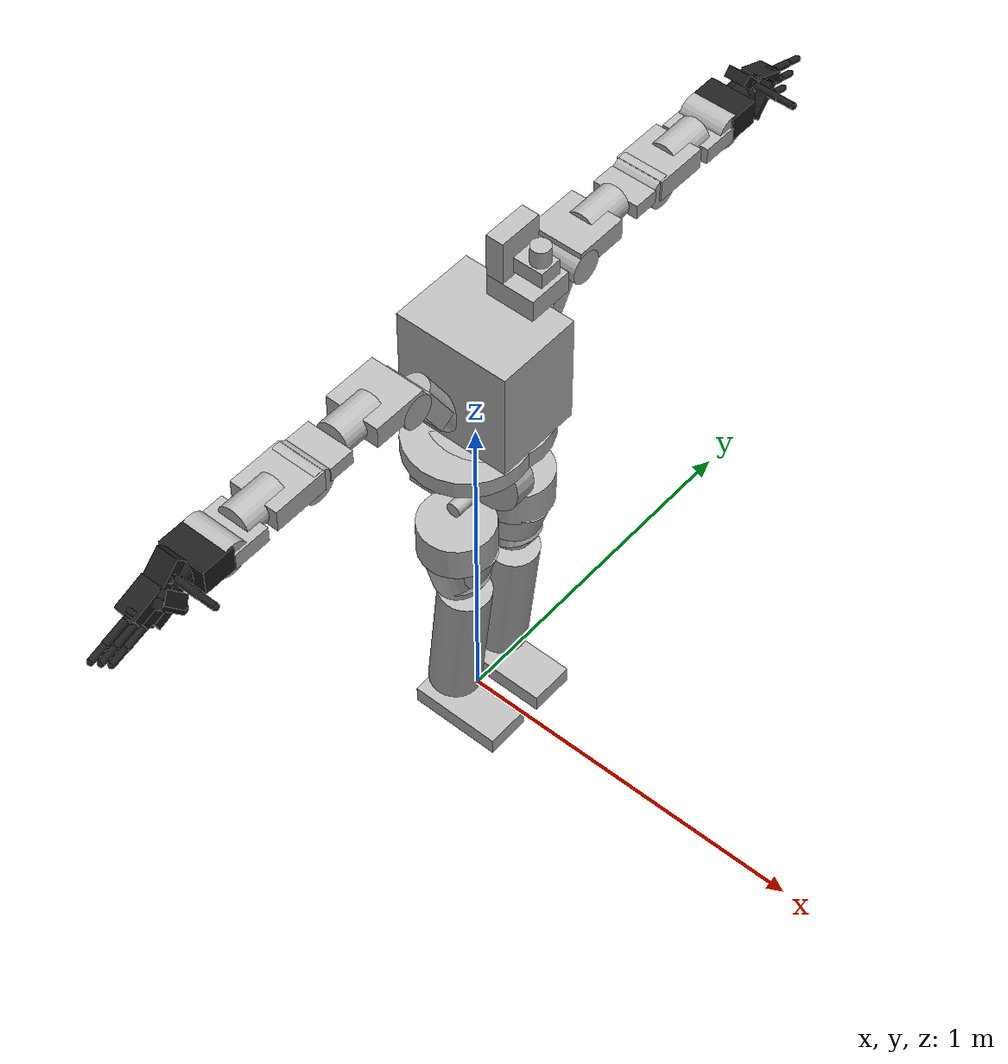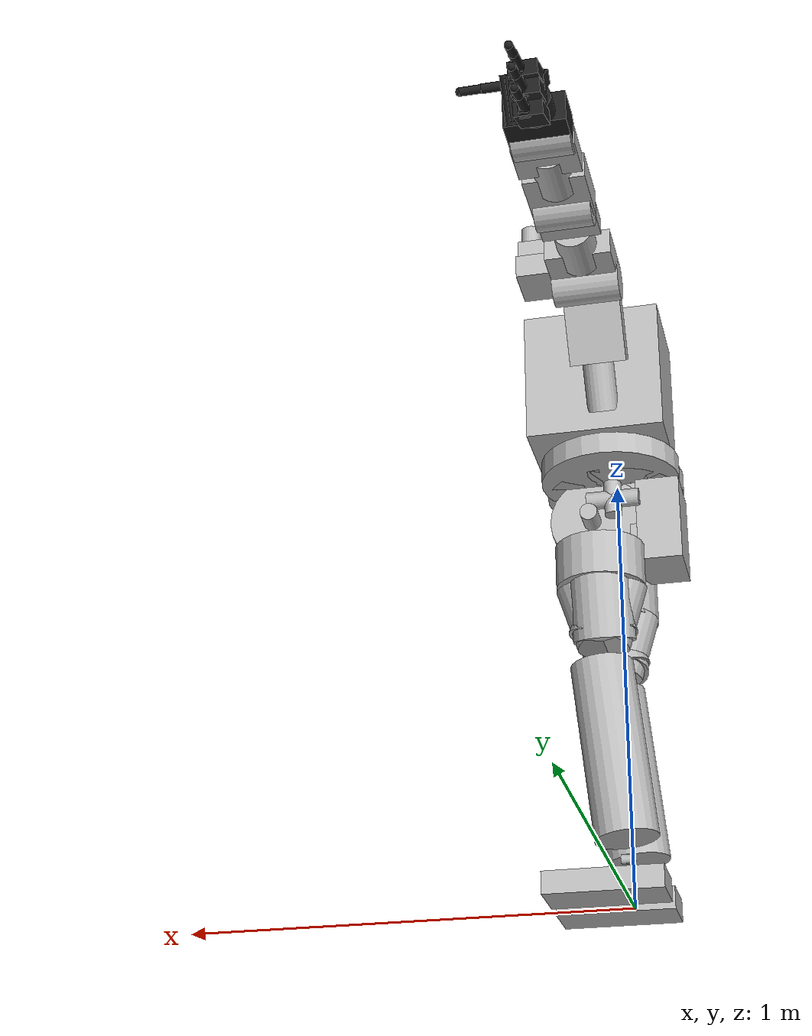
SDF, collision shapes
<sdf version='1.4'>
  <model name='atlas'>
    <link name='pelvis'>
      <pose>0.000000 0.000000 0.000000 0.000000 0.000000 0.000000</pose>
      <inertial>
        <pose>0.011486 0.000000 0.026774 0.000000 0.000000 0.000000</pose>
        <mass>12.646400</mass>
        <inertia>
          <ixx>0.033872</ixx>
          <ixy>0.000800</ixy>
          <ixz>-0.000500</ixz>
          <iyy>0.018823</iyy>
          <iyz>-0.000500</iyz>
          <izz>0.119295</izz>
        </inertia>
      </inertial>
      <collision name='pelvis_collision'>
        <pose>0.046000 0.000000 -0.020000 1.570800 0.000000 0.000000</pose>
        <geometry>
          <cylinder>
            <length>0.060000</length>
            <radius>0.110000</radius>
          </cylinder>
        </geometry>
        <surface>
          <contact>
            <ode/>
          </contact>
          <friction>
            <ode>
              <mu>0.900000</mu>
              <mu2>0.900000</mu2>
            </ode>
          </friction>
        </surface>
      </collision>
      <collision name='pelvis_collision_pelvis_other'>
        <pose>-0.030000 0.000000 -0.020000 1.570800 0.000000 0.000000</pose>
        <geometry>
          <cylinder>
            <length>0.060000</length>
            <radius>0.110000</radius>
          </cylinder>
        </geometry>
      </collision>
      <collision name='pelvis_collision_pelvis_other_1'>
        <pose>0.010000 0.042000 0.090000 0.000000 0.000000 0.000000</pose>
        <geometry>
          <cylinder>
            <length>0.050000</length>
            <radius>0.160000</radius>
          </cylinder>
        </geometry>
      </collision>
      <collision name='pelvis_collision_pelvis_other_2'>
        <pose>0.010000 -0.042000 0.090000 0.000000 0.000000 0.000000</pose>
        <geometry>
          <cylinder>
            <length>0.050000</length>
            <radius>0.160000</radius>
          </cylinder>
        </geometry>
      </collision>
      <collision name='pelvis_collision_pelvis_other_3'>
        <pose>-0.100000 0.000000 -0.050000 0.000000 0.000000 0.000000</pose>
        <geometry>
          <box>
            <size>0.100000 0.150000 0.200000</size>
          </box>
        </geometry>
      </collision>
      <visual name='pelvis_vis'>
        <pose>0.000000 0.000000 0.000000 0.000000 0.000000 0.000000</pose>
        <geometry>
          <mesh>
            <scale>1.000000 1.000000 1.000000</scale>
            <uri>model://atlas/meshes/pelvis.dae</uri>
          </mesh>
        </geometry>
      </visual>
      <visual name='pelvis_vis_imu_link'>
        <pose>0.059915 0.000000 -0.014150 0.000000 0.000000 0.000000</pose>
        <geometry>
          <box>
            <size>0.010000 0.010000 0.010000</size>
          </box>
        </geometry>
      </visual>
      <velocity_decay>
        <linear>0.000000</linear>
        <angular>0.000000</angular>
      </velocity_decay>
      <gravity>1</gravity>
      <velocity_decay>
        <linear>0.000000</linear>
        <angular>0.000000</angular>
      </velocity_decay>
      <self_collide>0</self_collide>
      <sensor name='imu_sensor' type='imu'>
        <always_on>1</always_on>
        <update_rate>1000.000000</update_rate>
        <imu>
          <noise>
            <type>gaussian</type>
            <rate>
              <mean>0.000000</mean>
              <stddev>0.000200</stddev>
              <bias_mean>0.000008</bias_mean>
              <bias_stddev>0.000001</bias_stddev>
            </rate>
            <accel>
              <mean>0.000000</mean>
              <stddev>0.017000</stddev>
              <bias_mean>0.100000</bias_mean>
              <bias_stddev>0.001000</bias_stddev>
            </accel>
          </noise>
        </imu>
        <pose>0.059915 0.000000 -0.014150 0.000000 0.000000 0.000000</pose>
      </sensor>
    </link>
    <link name='ltorso'>
      <pose>-0.012500 0.000000 0.000000 0.000000 0.000000 0.000000</pose>
      <inertial>
        <pose>-0.011298 -0.000003 0.074684 0.000000 0.000000 0.000000</pose>
        <mass>1.627290</mass>
        <inertia>
          <ixx>0.064665</ixx>
          <ixy>-0.000000</ixy>
          <ixz>-0.000342</ixz>
          <iyy>0.050298</iyy>
          <iyz>0.000000</iyz>
          <izz>0.109730</izz>
        </inertia>
      </inertial>
      <visual name='ltorso_vis'>
        <pose>0.000000 0.000000 0.000000 0.000000 0.000000 0.000000</pose>
        <geometry>
          <mesh>
            <scale>1.000000 1.000000 1.000000</scale>
            <uri>model://atlas/meshes/ltorso.dae</uri>
          </mesh>
        </geometry>
      </visual>
      <gravity>1</gravity>
      <velocity_decay>
        <linear>0.000000</linear>
        <angular>0.000000</angular>
      </velocity_decay>
      <self_collide>0</self_collide>
    </link>
    <joint name='back_lbz' type='revolute'>
      <child>ltorso</child>
      <parent>pelvis</parent>
      <axis>
        <xyz>0.000000 0.000000 1.000000</xyz>
        <limit>
          <lower>-0.610865</lower>
          <upper>0.610865</upper>
          <effort>124.016000</effort>
          <velocity>12.000000</velocity>
        </limit>
        <dynamics>
          <damping>10.000000</damping>
        </dynamics>
      </axis>
      <physics>
        <ode>
          <cfm_damping>1</cfm_damping>
          <limit>
            <cfm>0.000000</cfm>
            <erp>0.200000</erp>
          </limit>
        </ode>
      </physics>
    </joint>
    <link name='mtorso'>
      <pose>-0.012500 0.000000 0.090000 0.000000 0.000000 0.000000</pose>
      <inertial>
        <pose>-0.008163 -0.013125 0.030597 0.000000 0.000000 0.000000</pose>
        <mass>3.806800</mass>
        <inertia>
          <ixx>0.197500</ixx>
          <ixy>-0.000061</ixy>
          <ixz>0.000039</ixz>
          <iyy>0.544742</iyy>
          <iyz>0.000053</iyz>
          <izz>0.109730</izz>
        </inertia>
      </inertial>
      <collision name='mtorso_collision'>
        <pose>0.000000 0.000000 0.000000 1.570800 0.000000 0.000000</pose>
        <geometry>
          <cylinder>
            <length>0.030000</length>
            <radius>0.017000</radius>
          </cylinder>
        </geometry>
        <surface>
          <contact>
            <ode/>
          </contact>
          <friction>
            <ode>
              <mu>0.900000</mu>
              <mu2>0.900000</mu2>
            </ode>
          </friction>
        </surface>
      </collision>
      <collision name='mtorso_collision_mtorso_other'>
        <pose>0.028500 0.000000 0.050000 -0.000003 1.570793 -0.000003</pose>
        <geometry>
          <cylinder>
            <length>0.020000</length>
            <radius>0.015000</radius>
          </cylinder>
        </geometry>
      </collision>
      <collision name='mtorso_collision_mtorso_other_1'>
        <pose>-0.028500 0.000000 0.050000 -0.000003 1.570793 -0.000003</pose>
        <geometry>
          <cylinder>
            <length>0.020000</length>
            <radius>0.015000</radius>
          </cylinder>
        </geometry>
      </collision>
      <visual name='mtorso_vis'>
        <pose>0.000000 0.000000 0.000000 0.000000 0.000000 0.000000</pose>
        <geometry>
          <mesh>
            <scale>1.000000 1.000000 1.000000</scale>
            <uri>model://atlas/meshes/mtorso.dae</uri>
          </mesh>
        </geometry>
      </visual>
      <gravity>1</gravity>
      <velocity_decay>
        <linear>0.000000</linear>
        <angular>0.000000</angular>
      </velocity_decay>
      <self_collide>0</self_collide>
    </link>
    <joint name='back_mby' type='revolute'>
      <child>mtorso</child>
      <parent>ltorso</parent>
      <axis>
        <xyz>0.000000 1.000000 0.000000</xyz>
        <limit>
          <lower>-1.200000</lower>
          <upper>1.280000</upper>
          <effort>206.843000</effort>
          <velocity>12.000000</velocity>
        </limit>
        <dynamics>
          <damping>10.000000</damping>
        </dynamics>
      </axis>
      <physics>
        <ode>
          <cfm_damping>1</cfm_damping>
          <limit>
            <cfm>0.000000</cfm>
            <erp>0.200000</erp>
          </limit>
        </ode>
      </physics>
    </joint>
    <link name='utorso'>
      <pose>-0.012500 0.000000 0.140000 0.000000 0.000000 0.000000</pose>
      <inertial>
        <pose>0.020000 -0.001000 0.211000 0.000000 0.000000 0.000000</pose>
        <mass>15.227200</mass>
        <inertia>
          <ixx>0.395000</ixx>
          <ixy>0.000000</ixy>
          <ixz>0.083000</ixz>
          <iyy>0.544742</iyy>
          <iyz>-0.003000</iyz>
          <izz>0.109730</izz>
        </inertia>
      </inertial>
      <collision name='utorso_collision'>
        <pose>0.044600 0.000000 0.186900 0.000000 0.000000 0.000000</pose>
        <geometry>
          <box>
            <size>0.318800 0.240000 0.316200</size>
          </box>
        </geometry>
        <surface>
          <contact>
            <ode/>
          </contact>
          <friction>
            <ode>
              <mu>0.900000</mu>
              <mu2>0.900000</mu2>
            </ode>
          </friction>
        </surface>
      </collision>
      <collision name='utorso_collision_utorso_other'>
        <pose>0.024000 0.160000 0.180000 -0.523600 0.000000 0.000000</pose>
        <geometry>
          <cylinder>
            <length>0.223750</length>
            <radius>0.036300</radius>
          </cylinder>
        </geometry>
      </collision>
      <collision name='utorso_collision_utorso_other_1'>
        <pose>0.024000 -0.160000 0.180000 0.523600 0.000000 0.000000</pose>
        <geometry>
          <cylinder>
            <length>0.223750</length>
            <radius>0.036300</radius>
          </cylinder>
        </geometry>
      </collision>
      <visual name='utorso_vis'>
        <pose>0.000000 0.000000 0.000000 0.000000 0.000000 0.000000</pose>
        <geometry>
          <mesh>
            <scale>1.000000 1.000000 1.000000</scale>
            <uri>model://atlas/meshes/utorso.dae</uri>
          </mesh>
        </geometry>
      </visual>
      <gravity>1</gravity>
      <velocity_decay>
        <linear>0.000000</linear>
        <angular>0.000000</angular>
      </velocity_decay>
      <self_collide>0</self_collide>
    </link>
    <joint name='back_ubx' type='revolute'>
      <child>utorso</child>
      <parent>mtorso</parent>
      <axis>
        <xyz>1.000000 0.000000 0.000000</xyz>
        <limit>
          <lower>-0.790809</lower>
          <upper>0.790809</upper>
          <effort>94.910000</effort>
          <velocity>12.000000</velocity>
        </limit>
        <dynamics>
          <damping>10.000000</damping>
        </dynamics>
      </axis>
      <physics>
        <ode>
          <cfm_damping>1</cfm_damping>
          <limit>
            <cfm>0.000000</cfm>
            <erp>0.200000</erp>
          </limit>
        </ode>
      </physics>
    </joint>
    <link name='l_clav'>
      <pose>0.011500 0.221000 0.429000 0.000000 0.000000 0.000000</pose>
      <inertial>
        <pose>0.014000 0.058000 0.029000 0.000000 0.000000 0.000000</pose>
        <mass>2.369000</mass>
        <inertia>
          <ixx>0.004000</ixx>
          <ixy>0.001000</ixy>
          <ixz>0.000000</ixz>
          <iyy>0.006000</iyy>
          <iyz>0.000000</iyz>
          <izz>0.007000</izz>
        </inertia>
      </inertial>
      <collision name='l_clav_collision'>
        <pose>0.000000 0.069700 0.026100 -0.000003 1.570793 -0.000003</pose>
        <geometry>
          <cylinder>
            <length>0.152500</length>
            <radius>0.045000</radius>
          </cylinder>
        </geometry>
        <surface>
          <contact>
            <ode/>
          </contact>
          <friction>
            <ode>
              <mu>0.900000</mu>
              <mu2>0.900000</mu2>
            </ode>
          </friction>
        </surface>
      </collision>
      <collision name='l_clav_collision_l_clav_other'>
        <pose>-0.005000 -0.007400 -0.053800 1.047200 0.000000 0.000000</pose>
        <geometry>
          <box>
            <size>0.130000 0.150000 0.050000</size>
          </box>
        </geometry>
      </collision>
      <visual name='l_clav_vis'>
        <pose>0.000000 0.000000 0.000000 1.047200 0.000000 0.000000</pose>
        <geometry>
          <mesh>
            <scale>1.000000 1.000000 1.000000</scale>
            <uri>model://atlas/meshes/l_clav.dae</uri>
          </mesh>
        </geometry>
      </visual>
      <gravity>1</gravity>
      <velocity_decay>
        <linear>0.000000</linear>
        <angular>0.000000</angular>
      </velocity_decay>
      <self_collide>0</self_collide>
    </link>
    <joint name='l_arm_usy' type='revolute'>
      <child>l_clav</child>
      <parent>utorso</parent>
      <axis>
        <xyz>0.000000 0.500000 0.866025</xyz>
        <limit>
          <lower>-1.963500</lower>
          <upper>1.963500</upper>
          <effort>212.000000</effort>
          <velocity>12.000000</velocity>
        </limit>
        <dynamics>
          <damping>1.000000</damping>
        </dynamics>
      </axis>
      <physics>
        <ode>
          <cfm_damping>1</cfm_damping>
          <limit>
            <cfm>0.000000</cfm>
            <erp>0.200000</erp>
          </limit>
        </ode>
      </physics>
    </joint>
    <link name='l_scap'>
      <pose>0.011500 0.296000 0.465000 0.000000 0.000000 0.000000</pose>
      <inertial>
        <pose>-0.002000 0.108000 0.000000 0.000000 0.000000 0.000000</pose>
        <mass>2.707000</mass>
        <inertia>
          <ixx>0.010000</ixx>
          <ixy>0.000000</ixy>
          <ixz>0.000000</ixz>
          <iyy>0.005000</iyy>
          <iyz>0.000000</iyz>
          <izz>0.013000</izz>
        </inertia>
      </inertial>
      <collision name='l_scap_collision'>
        <pose>0.001000 0.126510 0.015210 1.570800 0.000000 0.000000</pose>
        <geometry>
          <cylinder>
            <length>0.125000</length>
            <radius>0.045000</radius>
          </cylinder>
        </geometry>
        <surface>
          <contact>
            <ode/>
          </contact>
          <friction>
            <ode>
              <mu>0.900000</mu>
              <mu2>0.900000</mu2>
            </ode>
          </friction>
        </surface>
      </collision>
      <collision name='l_scap_collision_l_scap_other'>
        <pose>0.001000 0.050000 0.016000 0.000000 0.000000 0.000000</pose>
        <geometry>
          <box>
            <size>0.150000 0.150000 0.060000</size>
          </box>
        </geometry>
      </collision>
      <visual name='l_scap_vis'>
        <pose>0.000000 0.000000 0.000000 0.000000 0.000000 0.000000</pose>
        <geometry>
          <mesh>
            <scale>1.000000 1.000000 1.000000</scale>
            <uri>model://atlas/meshes/l_scap.dae</uri>
          </mesh>
        </geometry>
      </visual>
      <gravity>1</gravity>
      <velocity_decay>
        <linear>0.000000</linear>
        <angular>0.000000</angular>
      </velocity_decay>
      <self_collide>0</self_collide>
    </link>
    <joint name='l_arm_shx' type='revolute'>
      <child>l_scap</child>
      <parent>l_clav</parent>
      <axis>
        <xyz>1.000000 0.000000 0.000000</xyz>
        <limit>
          <lower>-1.396260</lower>
          <upper>1.745330</upper>
          <effort>170.000000</effort>
          <velocity>12.000000</velocity>
        </limit>
        <dynamics>
          <damping>1.000000</damping>
        </dynamics>
      </axis>
      <physics>
        <ode>
          <cfm_damping>1</cfm_damping>
          <limit>
            <cfm>0.000000</cfm>
            <erp>0.200000</erp>
          </limit>
        </ode>
      </physics>
    </joint>
    <link name='l_uarm'>
      <pose>0.011500 0.481000 0.465000 0.000000 0.000000 0.000000</pose>
      <inertial>
        <pose>0.007000 0.114000 0.008000 0.000000 0.000000 0.000000</pose>
        <mass>1.881000</mass>
        <inertia>
          <ixx>0.002000</ixx>
          <ixy>0.000000</ixy>
          <ixz>0.000000</ixz>
          <iyy>0.003000</iyy>
          <iyz>0.000000</iyz>
          <izz>0.003000</izz>
        </inertia>
      </inertial>
      <collision name='l_uarm_collision'>
        <pose>0.001000 0.111000 0.000000 3.141590 1.570790 3.141590</pose>
        <geometry>
          <cylinder>
            <length>0.125000</length>
            <radius>0.045000</radius>
          </cylinder>
        </geometry>
        <surface>
          <contact>
            <ode/>
          </contact>
          <friction>
            <ode>
              <mu>0.900000</mu>
              <mu2>0.900000</mu2>
            </ode>
          </friction>
        </surface>
      </collision>
      <collision name='l_uarm_collision_l_uarm_other'>
        <pose>0.001000 0.043000 0.010000 -0.000003 1.570793 -0.000003</pose>
        <geometry>
          <box>
            <size>0.040000 0.070000 0.130000</size>
          </box>
        </geometry>
      </collision>
      <visual name='l_uarm_vis'>
        <pose>0.000000 0.000000 0.000000 0.000000 0.000000 0.000000</pose>
        <geometry>
          <mesh>
            <scale>1.000000 1.000000 1.000000</scale>
            <uri>model://atlas/meshes/l_uarm.dae</uri>
          </mesh>
        </geometry>
      </visual>
      <gravity>1</gravity>
      <velocity_decay>
        <linear>0.000000</linear>
        <angular>0.000000</angular>
      </velocity_decay>
      <self_collide>0</self_collide>
    </link>
    <joint name='l_arm_ely' type='revolute'>
      <child>l_uarm</child>
      <parent>l_scap</parent>
      <axis>
        <xyz>0.000000 1.000000 0.000000</xyz>
        <limit>
          <lower>0.000000</lower>
          <upper>3.141590</upper>
          <effort>114.000000</effort>
          <velocity>12.000000</velocity>
        </limit>
        <dynamics>
          <damping>1.000000</damping>
        </dynamics>
      </axis>
      <physics>
        <ode>
          <cfm_damping>1</cfm_damping>
          <limit>
            <cfm>0.000000</cfm>
            <erp>0.200000</erp>
          </limit>
        </ode>
      </physics>
    </joint>
    <link name='l_larm'>
      <pose>0.011500 0.602000 0.478000 0.000000 0.000000 0.000000</pose>
      <inertial>
        <pose>-0.003000 0.099000 -0.014000 0.000000 0.000000 0.000000</pose>
        <mass>2.148000</mass>
        <inertia>
          <ixx>0.005000</ixx>
          <ixy>0.000000</ixy>
          <ixz>0.000000</ixz>
          <iyy>0.003000</iyy>
          <iyz>0.000000</iyz>
          <izz>0.006000</izz>
        </inertia>
      </inertial>
      <collision name='l_larm_collision'>
        <pose>0.001000 0.127000 0.000000 1.570800 0.000000 0.000000</pose>
        <geometry>
          <cylinder>
            <length>0.125000</length>
            <radius>0.045000</radius>
          </cylinder>
        </geometry>
        <surface>
          <contact>
            <ode/>
          </contact>
          <friction>
            <ode>
              <mu>0.900000</mu>
              <mu2>0.900000</mu2>
            </ode>
          </friction>
        </surface>
      </collision>
      <collision name='l_larm_collision_l_larm_other'>
        <pose>0.001000 0.051000 0.000000 0.000000 0.000000 0.000000</pose>
        <geometry>
          <box>
            <size>0.135000 0.150000 0.060000</size>
          </box>
        </geometry>
      </collision>
      <visual name='l_larm_vis'>
        <pose>0.000000 0.000000 0.000000 0.000000 0.000000 0.000000</pose>
        <geometry>
          <mesh>
            <scale>1.000000 1.000000 1.000000</scale>
            <uri>model://atlas/meshes/l_larm.dae</uri>
          </mesh>
        </geometry>
      </visual>
      <gravity>1</gravity>
      <velocity_decay>
        <linear>0.000000</linear>
        <angular>0.000000</angular>
      </velocity_decay>
      <self_collide>0</self_collide>
    </link>
    <joint name='l_arm_elx' type='revolute'>
      <child>l_larm</child>
      <parent>l_uarm</parent>
      <axis>
        <xyz>1.000000 0.000000 0.000000</xyz>
        <limit>
          <lower>0.000000</lower>
          <upper>2.356190</upper>
          <effort>114.000000</effort>
          <velocity>12.000000</velocity>
        </limit>
        <dynamics>
          <damping>1.000000</damping>
        </dynamics>
      </axis>
      <physics>
        <ode>
          <cfm_damping>1</cfm_damping>
          <limit>
            <cfm>0.000000</cfm>
            <erp>0.200000</erp>
          </limit>
        </ode>
      </physics>
    </joint>
    <link name='l_farm'>
      <pose>0.011500 0.790000 0.465000 0.000000 0.000000 0.000000</pose>
      <inertial>
        <pose>0.000000 0.041000 0.000000 0.000000 0.000000 0.000000</pose>
        <mass>0.981000</mass>
        <inertia>
          <ixx>0.003000</ixx>
          <ixy>0.000000</ixy>
          <ixz>0.000000</ixz>
          <iyy>0.001000</iyy>
          <iyz>0.000000</iyz>
          <izz>0.003000</izz>
        </inertia>
      </inertial>
      <collision name='l_farm_collision'>
        <pose>0.000000 0.065000 0.004000 3.141590 1.570790 3.141590</pose>
        <geometry>
          <cylinder>
            <length>0.125000</length>
            <radius>0.045000</radius>
          </cylinder>
        </geometry>
        <surface>
          <contact>
            <ode/>
          </contact>
          <friction>
            <ode>
              <mu>0.900000</mu>
              <mu2>0.900000</mu2>
            </ode>
          </friction>
        </surface>
      </collision>
      <collision name='l_farm_collision_l_farm_other'>
        <pose>0.001000 0.015000 -0.002000 0.000000 0.000000 0.000000</pose>
        <geometry>
          <box>
            <size>0.135000 0.100000 0.045000</size>
          </box>
        </geometry>
      </collision>
      <visual name='l_farm_vis'>
        <pose>0.000000 -0.060000 0.000000 0.000000 0.000000 0.000000</pose>
        <geometry>
          <mesh>
            <scale>1.000000 1.000000 1.000000</scale>
            <uri>model://atlas/meshes/l_farm.dae</uri>
          </mesh>
        </geometry>
      </visual>
      <gravity>1</gravity>
      <velocity_decay>
        <linear>0.000000</linear>
        <angular>0.000000</angular>
      </velocity_decay>
      <self_collide>0</self_collide>
    </link>
    <joint name='l_arm_uwy' type='revolute'>
      <child>l_farm</child>
      <parent>l_larm</parent>
      <axis>
        <xyz>0.000000 1.000000 0.000000</xyz>
        <limit>
          <lower>-1.571000</lower>
          <upper>1.571000</upper>
          <effort>114.000000</effort>
          <velocity>12.000000</velocity>
        </limit>
        <dynamics>
          <damping>1.000000</damping>
        </dynamics>
      </axis>
      <physics>
        <ode>
          <cfm_damping>1</cfm_damping>
          <limit>
            <cfm>0.000000</cfm>
            <erp>0.200000</erp>
          </limit>
        </ode>
      </physics>
    </joint>
    <link name='l_hand'>
      <pose>0.011500 0.848000 0.465000 0.000000 0.000000 0.000000</pose>
      <inertial>
        <pose>0.021445 0.093647 0.000895 0.000000 0.000000 0.000000</pose>
        <mass>4.626000</mass>
        <inertia>
          <ixx>0.018261</ixx>
          <ixy>-0.000218</ixy>
          <ixz>0.001270</ixz>
          <iyy>0.013959</iyy>
          <iyz>0.000005</iyz>
          <izz>0.015384</izz>
        </inertia>
      </inertial>
      <collision name='l_hand_collision'>
        <pose>0.001000 0.100000 0.010000 1.570800 0.000000 0.000000</pose>
        <geometry>
          <cylinder>
            <length>0.050000</length>
            <radius>0.030000</radius>
          </cylinder>
        </geometry>
        <surface>
          <contact>
            <ode/>
          </contact>
          <friction>
            <ode/>
          </friction>
        </surface>
        <surface>
          <contact>
            <ode/>
          </contact>
          <friction>
            <ode>
              <mu>0.900000</mu>
              <mu2>0.900000</mu2>
            </ode>
          </friction>
        </surface>
      </collision>
      <collision name='l_hand_collision_left_palm'>
        <pose>0.038001 0.169000 -0.016000 0.670796 0.000006 3.141590</pose>
        <geometry>
          <cylinder>
            <length>0.100000</length>
            <radius>0.013000</radius>
          </cylinder>
        </geometry>
        <max_contacts>6</max_contacts>
        <surface>
          <contact>
            <ode>
              <kp>1000000.000000</kp>
              <kd>1.000000</kd>
              <max_vel>0.100000</max_vel>
              <min_depth>0.000000</min_depth>
            </ode>
          </contact>
          <friction>
            <ode>
              <mu>1.100000</mu>
              <mu2>1.100000</mu2>
            </ode>
          </friction>
        </surface>
      </collision>
      <collision name='l_hand_collision_left_palm_1'>
        <pose>0.021001 0.164000 -0.008000 1.980790 -0.900000 1.570800</pose>
        <geometry>
          <box>
            <size>0.090000 0.035000 0.050000</size>
          </box>
        </geometry>
      </collision>
      <collision name='l_hand_collision_left_palm_2'>
        <pose>-0.005000 0.120000 -0.000000 1.570800 0.000006 3.141590</pose>
        <geometry>
          <cylinder>
            <length>0.050000</length>
            <radius>0.038000</radius>
          </cylinder>
        </geometry>
      </collision>
      <collision name='l_hand_collision_left_palm_3'>
        <pose>-0.004999 0.210000 0.010000 1.570790 0.370000 1.570790</pose>
        <geometry>
          <box>
            <size>0.090000 0.030000 0.060000</size>
          </box>
        </geometry>
      </collision>
      <collision name='l_hand_collision_left_palm_4'>
        <pose>-0.004999 0.190000 -0.020000 1.570790 0.370000 1.570790</pose>
        <geometry>
          <box>
            <size>0.090000 0.030000 0.060000</size>
          </box>
        </geometry>
      </collision>
      <collision name='l_hand_collision_left_palm_5'>
        <pose>-0.004999 0.160000 -0.050000 1.570790 0.370000 1.570790</pose>
        <geometry>
          <box>
            <size>0.090000 0.030000 0.060000</size>
          </box>
        </geometry>
      </collision>
      <collision name='l_hand_collision_left_palm_6'>
        <pose>-0.005000 0.144000 0.040000 1.570790 0.790000 1.570780</pose>
        <geometry>
          <box>
            <size>0.090000 0.030000 0.060000</size>
          </box>
        </geometry>
      </collision>
      <collision name='l_hand_collision_l_hand_other'>
        <pose>0.001000 0.050000 0.010000 0.000000 0.000000 0.000000</pose>
        <geometry>
          <box>
            <size>0.130000 0.090000 0.070000</size>
          </box>
        </geometry>
      </collision>
      <visual name='l_hand_vis'>
        <pose>0.000000 0.000000 0.000000 0.000000 0.000000 0.000000</pose>
        <geometry>
          <mesh>
            <scale>1.000000 1.000000 1.000000</scale>
            <uri>model://atlas/meshes/l_hand.dae</uri>
          </mesh>
        </geometry>
      </visual>
      <visual name='l_hand_vis_left_palm'>
        <pose>0.038001 0.169000 -0.016000 0.670796 0.000006 3.141590</pose>
        <geometry>
          <cylinder>
            <length>0.100000</length>
            <radius>0.013000</radius>
          </cylinder>
        </geometry>
        <material>
          <script>
            <name>Gazebo/FlatBlack</name>
            <uri>__default__</uri>
          </script>
        </material>
      </visual>
      <visual name='l_hand_vis_left_palm_1'>
        <pose>0.021001 0.164000 -0.008000 1.980790 -0.900000 1.570800</pose>
        <geometry>
          <box>
            <size>0.090000 0.035000 0.050000</size>
          </box>
        </geometry>
        <material>
          <script>
            <name>Gazebo/FlatBlack</name>
            <uri>__default__</uri>
          </script>
        </material>
      </visual>
      <visual name='l_hand_vis_left_palm_2'>
        <pose>-0.005000 0.120000 -0.000000 1.570800 0.000006 3.141590</pose>
        <geometry>
          <cylinder>
            <length>0.050000</length>
            <radius>0.038000</radius>
          </cylinder>
        </geometry>
        <material>
          <script>
            <name>Gazebo/FlatBlack</name>
            <uri>__default__</uri>
          </script>
        </material>
      </visual>
      <visual name='l_hand_vis_left_palm_3'>
        <pose>-0.004999 0.210000 0.010000 1.570790 0.370000 1.570790</pose>
        <geometry>
          <box>
            <size>0.090000 0.030000 0.060000</size>
          </box>
        </geometry>
        <material>
          <script>
            <name>Gazebo/FlatBlack</name>
            <uri>__default__</uri>
          </script>
        </material>
      </visual>
      <visual name='l_hand_vis_left_palm_4'>
        <pose>-0.004999 0.190000 -0.020000 1.570790 0.370000 1.570790</pose>
        <geometry>
          <box>
            <size>0.090000 0.030000 0.060000</size>
          </box>
        </geometry>
        <material>
          <script>
            <name>Gazebo/FlatBlack</name>
            <uri>__default__</uri>
          </script>
        </material>
      </visual>
      <visual name='l_hand_vis_left_palm_5'>
        <pose>-0.004999 0.160000 -0.050000 1.570790 0.370000 1.570790</pose>
        <geometry>
          <box>
            <size>0.090000 0.030000 0.060000</size>
          </box>
        </geometry>
        <material>
          <script>
            <name>Gazebo/FlatBlack</name>
            <uri>__default__</uri>
          </script>
        </material>
      </visual>
      <visual name='l_hand_vis_left_palm_6'>
        <pose>-0.005000 0.144000 0.040000 1.570790 0.790000 1.570780</pose>
        <geometry>
          <box>
            <size>0.090000 0.030000 0.060000</size>
          </box>
        </geometry>
        <material>
          <script>
            <name>Gazebo/FlatBlack</name>
            <uri>__default__</uri>
          </script>
        </material>
      </visual>
      <visual name='l_hand_vis_left_palm_left_camera_frame'>
        <pose>0.025001 0.143513 -0.045167 -2.241600 -0.000006 -0.000006</pose>
        <geometry>
          <box>
            <size>0.003000 0.010000 0.007000</size>
          </box>
        </geometry>
        <material>
          <script>
            <name>Gazebo/FlatBlack</name>
            <uri>__default__</uri>
          </script>
        </material>
      </visual>
      <visual name='l_hand_vis_left_palm_right_camera_frame'>
        <pose>0.025001 0.168377 -0.013834 -2.241600 -0.000006 -0.000006</pose>
        <geometry>
          <box>
            <size>0.003000 0.010000 0.007000</size>
          </box>
        </geometry>
        <material>
          <script>
            <name>Gazebo/FlatBlack</name>
            <uri>__default__</uri>
          </script>
        </material>
      </visual>
      <velocity_decay>
        <linear>0.000000</linear>
        <angular>0.000000</angular>
      </velocity_decay>
      <sensor name='imu_sensor' type='imu'>
        <always_on>1</always_on>
        <update_rate>1000.000000</update_rate>
        <imu>
          <noise>
            <type>gaussian</type>
            <rate>
              <mean>0.000000</mean>
              <stddev>0.000200</stddev>
              <bias_mean>0.000008</bias_mean>
              <bias_stddev>0.000001</bias_stddev>
            </rate>
            <accel>
              <mean>0.000000</mean>
              <stddev>0.017000</stddev>
              <bias_mean>0.100000</bias_mean>
              <bias_stddev>0.001000</bias_stddev>
            </accel>
          </noise>
        </imu>
      </sensor>
      <velocity_decay>
        <linear>0.000000</linear>
        <angular>0.000000</angular>
      </velocity_decay>
      <velocity_decay>
        <linear>0.000000</linear>
        <angular>0.000000</angular>
      </velocity_decay>
      <velocity_decay>
        <linear>0.000000</linear>
        <angular>0.000000</angular>
      </velocity_decay>
      <velocity_decay>
        <linear>0.000000</linear>
        <angular>0.000000</angular>
      </velocity_decay>
      <velocity_decay>
        <linear>0.000000</linear>
        <angular>0.000000</angular>
      </velocity_decay>
      <velocity_decay>
        <linear>0.000000</linear>
        <angular>0.000000</angular>
      </velocity_decay>
      <gravity>1</gravity>
      <velocity_decay>
        <linear>0.000000</linear>
        <angular>0.000000</angular>
      </velocity_decay>
      <self_collide>0</self_collide>
      <sensor name='left_palm_stereo_camera' type='multicamera'>
        <update_rate>30.000000</update_rate>
        <camera name='left'>
          <horizontal_fov>1.256637</horizontal_fov>
          <image>
            <width>752</width>
            <height>480</height>
            <format>L8</format>
          </image>
          <clip>
            <near>0.020000</near>
            <far>100.000000</far>
          </clip>
          <noise>
            <type>gaussian</type>
            <mean>0.000000</mean>
            <stddev>0.007000</stddev>
          </noise>
        </camera>
        <camera name='right'>
          <pose>0.000000 -0.040000 0.000000 0.000000 0.000000 0.000000</pose>
          <horizontal_fov>1.256637</horizontal_fov>
          <image>
            <width>752</width>
            <height>480</height>
            <format>L8</format>
          </image>
          <clip>
            <near>0.020000</near>
            <far>100.000000</far>
          </clip>
          <noise>
            <type>gaussian</type>
            <mean>0.000000</mean>
            <stddev>0.007000</stddev>
          </noise>
        </camera>
        <plugin name='stereo_camera_controller' filename='libgazebo_ros_multicamera.so'>
          <alwaysOn>1</alwaysOn>
          <updateRate>0.0</updateRate>
          <cameraName>sandia_hands/l_hand/camera</cameraName>
          <imageTopicName>image_raw</imageTopicName>
          <cameraInfoTopicName>camera_info</cameraInfoTopicName>
          <frameName>left_palm_left_camera_optical_frame</frameName>
          <hackBaseline>0.04</hackBaseline>
          <distortionK1>0.0</distortionK1>
          <distortionK2>0.0</distortionK2>
          <distortionK3>0.0</distortionK3>
          <distortionT1>0.0</distortionT1>
          <distortionT2>0.0</distortionT2>
        </plugin>
        <pose>0.025001 0.143513 -0.045167 -2.241600 -0.000006 -0.000006</pose>
      </sensor>
    </link>
    <joint name='l_arm_mwx' type='revolute'>
      <child>l_hand</child>
      <parent>l_farm</parent>
      <axis>
        <xyz>1.000000 0.000000 0.000000</xyz>
        <limit>
          <lower>-0.436000</lower>
          <upper>1.571000</upper>
          <effort>60.000000</effort>
          <velocity>12.000000</velocity>
        </limit>
        <dynamics>
          <damping>1.000000</damping>
        </dynamics>
      </axis>
      <physics>
        <ode>
          <provide_feedback>1</provide_feedback>
          <limit>
            <cfm>0.000000</cfm>
            <erp>0.200000</erp>
          </limit>
          <cfm_damping>1</cfm_damping>
        </ode>
      </physics>
    </joint>
    <link name='left_f0_0'>
      <pose>0.011501 1.088000 0.465000 1.570790 0.300000 1.570790</pose>
      <inertial>
        <pose>0.000000 0.000000 0.000000 0.000000 0.000000 0.000000</pose>
        <mass>0.106000</mass>
        <inertia>
          <ixx>0.000012</ixx>
          <ixy>0.000000</ixy>
          <ixz>0.000000</ixz>
          <iyy>0.000115</iyy>
          <iyz>0.000000</iyz>
          <izz>0.000115</izz>
        </inertia>
      </inertial>
      <collision name='left_f0_0_collision'>
        <pose>0.000000 0.000000 0.003000 0.000000 0.000000 0.000000</pose>
        <geometry>
          <cylinder>
            <length>0.023000</length>
            <radius>0.015000</radius>
          </cylinder>
        </geometry>
        <max_contacts>1</max_contacts>
        <surface>
          <contact>
            <ode>
              <kp>1000000.000000</kp>
              <kd>10.000000</kd>
              <max_vel>0.100000</max_vel>
              <min_depth>0.000000</min_depth>
            </ode>
          </contact>
          <friction>
            <ode>
              <mu>1.100000</mu>
              <mu2>1.100000</mu2>
            </ode>
          </friction>
        </surface>
      </collision>
      <collision name='left_f0_0_collision_left_f0_0_other'>
        <pose>0.011000 0.000000 0.003000 1.570800 0.000000 0.000000</pose>
        <geometry>
          <cylinder>
            <length>0.023000</length>
            <radius>0.010000</radius>
          </cylinder>
        </geometry>
      </collision>
      <visual name='left_f0_0_vis'>
        <pose>0.000000 0.000000 0.003000 0.000000 0.000000 0.000000</pose>
        <geometry>
          <cylinder>
            <length>0.023000</length>
            <radius>0.015000</radius>
          </cylinder>
        </geometry>
        <material>
          <script>
            <name>Gazebo/FlatBlack</name>
            <uri>__default__</uri>
          </script>
        </material>
      </visual>
      <visual name='left_f0_0_vis_left_f0_0_1'>
        <pose>0.011000 0.000000 0.003000 1.570800 0.000000 0.000000</pose>
        <geometry>
          <cylinder>
            <length>0.023000</length>
            <radius>0.010000</radius>
          </cylinder>
        </geometry>
        <material>
          <script>
            <name>Gazebo/FlatBlack</name>
            <uri>__default__</uri>
          </script>
        </material>
      </visual>
      <gravity>1</gravity>
      <velocity_decay>
        <linear>0.000000</linear>
        <angular>0.000000</angular>
      </velocity_decay>
      <self_collide>0</self_collide>
    </link>
    <joint name='left_f0_j0' type='revolute'>
      <child>left_f0_0</child>
      <parent>l_hand</parent>
      <axis>
        <xyz>-1.000000 0.000006 -0.000006</xyz>
        <limit>
          <lower>-1.570800</lower>
          <upper>1.570800</upper>
          <effort>11.000000</effort>
          <velocity>-1.000000</velocity>
        </limit>
        <dynamics>
          <damping>1.000000</damping>
        </dynamics>
      </axis>
      <physics>
        <ode>
          <cfm_damping>1</cfm_damping>
          <limit>
            <cfm>0.000000</cfm>
            <erp>0.200000</erp>
          </limit>
        </ode>
      </physics>
    </joint>
    <link name='left_f0_1'>
      <pose>0.011501 1.114750 0.456725 3.141590 0.300000 1.570790</pose>
      <inertial>
        <pose>0.006977 0.000000 0.000000 0.000000 0.000000 0.000000</pose>
        <mass>0.043000</mass>
        <inertia>
          <ixx>0.000003</ixx>
          <ixy>0.000000</ixy>
          <ixz>0.000000</ixz>
          <iyy>0.000021</iyy>
          <iyz>0.000000</iyz>
          <izz>0.000021</izz>
        </inertia>
      </inertial>
      <collision name='left_f0_1_collision'>
        <pose>0.024000 0.000000 0.000000 3.141593 1.570793 3.141593</pose>
        <geometry>
          <cylinder>
            <length>0.067000</length>
            <radius>0.010000</radius>
          </cylinder>
        </geometry>
        <max_contacts>1</max_contacts>
        <surface>
          <contact>
            <ode>
              <kp>1000000.000000</kp>
              <kd>10.000000</kd>
              <max_vel>0.100000</max_vel>
              <min_depth>0.000000</min_depth>
            </ode>
          </contact>
          <friction>
            <ode>
              <mu>1.100000</mu>
              <mu2>1.100000</mu2>
            </ode>
          </friction>
        </surface>
      </collision>
      <visual name='left_f0_1_vis'>
        <pose>0.024000 0.000000 0.000000 3.141593 1.570793 3.141593</pose>
        <geometry>
          <cylinder>
            <length>0.067000</length>
            <radius>0.010000</radius>
          </cylinder>
        </geometry>
        <material>
          <script>
            <name>Gazebo/FlatBlack</name>
            <uri>__default__</uri>
          </script>
        </material>
      </visual>
      <gravity>1</gravity>
      <velocity_decay>
        <linear>0.000000</linear>
        <angular>0.000000</angular>
      </velocity_decay>
      <self_collide>0</self_collide>
    </link>
    <joint name='left_f0_j1' type='revolute'>
      <child>left_f0_1</child>
      <parent>left_f0_0</parent>
      <axis>
        <xyz>0.000004 -0.295520 -0.955336</xyz>
        <limit>
          <lower>-1.570800</lower>
          <upper>1.570800</upper>
          <effort>28.000000</effort>
          <velocity>-1.000000</velocity>
        </limit>
        <dynamics>
          <damping>1.000000</damping>
        </dynamics>
      </axis>
      <physics>
        <ode>
          <cfm_damping>1</cfm_damping>
          <limit>
            <cfm>0.000000</cfm>
            <erp>0.200000</erp>
          </limit>
        </ode>
      </physics>
    </joint>
    <link name='left_f0_2'>
      <pose>0.011502 1.162520 0.441949 3.141590 0.300000 1.570790</pose>
      <inertial>
        <pose>0.009302 0.000000 0.000000 0.000000 0.000000 0.000000</pose>
        <mass>0.043000</mass>
        <inertia>
          <ixx>0.000002</ixx>
          <ixy>0.000000</ixy>
          <ixz>0.000000</ixz>
          <iyy>0.000023</iyy>
          <iyz>0.000000</iyz>
          <izz>0.000023</izz>
        </inertia>
      </inertial>
      <collision name='left_f0_2_collision'>
        <pose>0.024000 0.000000 0.000000 3.141593 1.570793 3.141593</pose>
        <geometry>
          <cylinder>
            <length>0.057000</length>
            <radius>0.009000</radius>
          </cylinder>
        </geometry>
        <max_contacts>1</max_contacts>
        <surface>
          <contact>
            <ode>
              <kp>1000000.000000</kp>
              <kd>10.000000</kd>
              <max_vel>0.100000</max_vel>
              <min_depth>0.000000</min_depth>
            </ode>
          </contact>
          <friction>
            <ode>
              <mu>1.100000</mu>
              <mu2>1.100000</mu2>
            </ode>
          </friction>
        </surface>
      </collision>
      <collision name='left_f0_2_collision_left_f0_2_other'>
        <pose>0.052000 0.000000 0.000000 0.000000 0.000000 0.000000</pose>
        <geometry>
          <sphere>
            <radius>0.009000</radius>
          </sphere>
        </geometry>
      </collision>
      <visual name='left_f0_2_vis'>
        <pose>0.024000 0.000000 0.000000 3.141593 1.570793 3.141593</pose>
        <geometry>
          <cylinder>
            <length>0.057000</length>
            <radius>0.009000</radius>
          </cylinder>
        </geometry>
        <material>
          <script>
            <name>Gazebo/FlatBlack</name>
            <uri>__default__</uri>
          </script>
        </material>
      </visual>
      <visual name='left_f0_2_vis_left_f0_2_1'>
        <pose>0.052000 0.000000 0.000000 0.000000 0.000000 0.000000</pose>
        <geometry>
          <sphere>
            <radius>0.009000</radius>
          </sphere>
        </geometry>
        <material>
          <script>
            <name>Gazebo/FlatBlack</name>
            <uri>__default__</uri>
          </script>
        </material>
      </visual>
      <gravity>1</gravity>
      <velocity_decay>
        <linear>0.000000</linear>
        <angular>0.000000</angular>
      </velocity_decay>
      <self_collide>0</self_collide>
    </link>
    <joint name='left_f0_j2' type='revolute'>
      <child>left_f0_2</child>
      <parent>left_f0_1</parent>
      <axis>
        <xyz>0.000004 -0.295520 -0.955336</xyz>
        <limit>
          <lower>-1.570800</lower>
          <upper>1.570800</upper>
          <effort>28.000000</effort>
          <velocity>-1.000000</velocity>
        </limit>
        <dynamics>
          <damping>1.000000</damping>
        </dynamics>
      </axis>
      <physics>
        <ode>
          <cfm_damping>1</cfm_damping>
          <limit>
            <cfm>0.000000</cfm>
            <erp>0.200000</erp>
          </limit>
        </ode>
      </physics>
    </joint>
    <link name='left_f1_0'>
      <pose>0.011501 1.063000 0.433780 1.570790 0.300000 1.570790</pose>
      <inertial>
        <pose>0.000000 0.000000 0.000000 0.000000 0.000000 0.000000</pose>
        <mass>0.106000</mass>
        <inertia>
          <ixx>0.000012</ixx>
          <ixy>0.000000</ixy>
          <ixz>0.000000</ixz>
          <iyy>0.000115</iyy>
          <iyz>0.000000</iyz>
          <izz>0.000115</izz>
        </inertia>
      </inertial>
      <collision name='left_f1_0_collision'>
        <pose>0.000000 0.000000 0.003000 0.000000 0.000000 0.000000</pose>
        <geometry>
          <cylinder>
            <length>0.023000</length>
            <radius>0.015000</radius>
          </cylinder>
        </geometry>
        <max_contacts>1</max_contacts>
        <surface>
          <contact>
            <ode>
              <kp>1000000.000000</kp>
              <kd>10.000000</kd>
              <max_vel>0.100000</max_vel>
              <min_depth>0.000000</min_depth>
            </ode>
          </contact>
          <friction>
            <ode>
              <mu>1.100000</mu>
              <mu2>1.100000</mu2>
            </ode>
          </friction>
        </surface>
      </collision>
      <collision name='left_f1_0_collision_left_f1_0_other'>
        <pose>0.011000 0.000000 0.003000 1.570800 0.000000 0.000000</pose>
        <geometry>
          <cylinder>
            <length>0.023000</length>
            <radius>0.010000</radius>
          </cylinder>
        </geometry>
      </collision>
      <visual name='left_f1_0_vis'>
        <pose>0.000000 0.000000 0.003000 0.000000 0.000000 0.000000</pose>
        <geometry>
          <cylinder>
            <length>0.023000</length>
            <radius>0.015000</radius>
          </cylinder>
        </geometry>
        <material>
          <script>
            <name>Gazebo/FlatBlack</name>
            <uri>__default__</uri>
          </script>
        </material>
      </visual>
      <visual name='left_f1_0_vis_left_f1_0_1'>
        <pose>0.011000 0.000000 0.003000 1.570800 0.000000 0.000000</pose>
        <geometry>
          <cylinder>
            <length>0.023000</length>
            <radius>0.010000</radius>
          </cylinder>
        </geometry>
        <material>
          <script>
            <name>Gazebo/FlatBlack</name>
            <uri>__default__</uri>
          </script>
        </material>
      </visual>
      <gravity>1</gravity>
      <velocity_decay>
        <linear>0.000000</linear>
        <angular>0.000000</angular>
      </velocity_decay>
      <self_collide>0</self_collide>
    </link>
    <joint name='left_f1_j0' type='revolute'>
      <child>left_f1_0</child>
      <parent>l_hand</parent>
      <axis>
        <xyz>-1.000000 0.000006 -0.000006</xyz>
        <limit>
          <lower>-1.570800</lower>
          <upper>1.570800</upper>
          <effort>11.000000</effort>
          <velocity>-1.000000</velocity>
        </limit>
        <dynamics>
          <damping>1.000000</damping>
        </dynamics>
      </axis>
      <physics>
        <ode>
          <cfm_damping>1</cfm_damping>
          <limit>
            <cfm>0.000000</cfm>
            <erp>0.200000</erp>
          </limit>
        </ode>
      </physics>
    </joint>
    <link name='left_f1_1'>
      <pose>0.011501 1.089750 0.425505 3.141590 0.300000 1.570790</pose>
      <inertial>
        <pose>0.006977 0.000000 0.000000 0.000000 0.000000 0.000000</pose>
        <mass>0.043000</mass>
        <inertia>
          <ixx>0.000003</ixx>
          <ixy>0.000000</ixy>
          <ixz>0.000000</ixz>
          <iyy>0.000021</iyy>
          <iyz>0.000000</iyz>
          <izz>0.000021</izz>
        </inertia>
      </inertial>
      <collision name='left_f1_1_collision'>
        <pose>0.024000 0.000000 0.000000 3.141593 1.570793 3.141593</pose>
        <geometry>
          <cylinder>
            <length>0.067000</length>
            <radius>0.010000</radius>
          </cylinder>
        </geometry>
        <max_contacts>1</max_contacts>
        <surface>
          <contact>
            <ode>
              <kp>1000000.000000</kp>
              <kd>10.000000</kd>
              <max_vel>0.100000</max_vel>
              <min_depth>0.000000</min_depth>
            </ode>
          </contact>
          <friction>
            <ode>
              <mu>1.100000</mu>
              <mu2>1.100000</mu2>
            </ode>
          </friction>
        </surface>
      </collision>
      <visual name='left_f1_1_vis'>
        <pose>0.024000 0.000000 0.000000 3.141593 1.570793 3.141593</pose>
        <geometry>
          <cylinder>
            <length>0.067000</length>
            <radius>0.010000</radius>
          </cylinder>
        </geometry>
        <material>
          <script>
            <name>Gazebo/FlatBlack</name>
            <uri>__default__</uri>
          </script>
        </material>
      </visual>
      <gravity>1</gravity>
      <velocity_decay>
        <linear>0.000000</linear>
        <angular>0.000000</angular>
      </velocity_decay>
      <self_collide>0</self_collide>
    </link>
    <joint name='left_f1_j1' type='revolute'>
      <child>left_f1_1</child>
      <parent>left_f1_0</parent>
      <axis>
        <xyz>0.000004 -0.295520 -0.955336</xyz>
        <limit>
          <lower>-1.570800</lower>
          <upper>1.570800</upper>
          <effort>28.000000</effort>
          <velocity>-1.000000</velocity>
        </limit>
        <dynamics>
          <damping>1.000000</damping>
        </dynamics>
      </axis>
      <physics>
        <ode>
          <cfm_damping>1</cfm_damping>
          <limit>
            <cfm>0.000000</cfm>
            <erp>0.200000</erp>
          </limit>
        </ode>
      </physics>
    </joint>
    <link name='left_f1_2'>
      <pose>0.011502 1.137520 0.410729 3.141590 0.300000 1.570790</pose>
      <inertial>
        <pose>0.009302 0.000000 0.000000 0.000000 0.000000 0.000000</pose>
        <mass>0.043000</mass>
        <inertia>
          <ixx>0.000002</ixx>
          <ixy>0.000000</ixy>
          <ixz>0.000000</ixz>
          <iyy>0.000023</iyy>
          <iyz>0.000000</iyz>
          <izz>0.000023</izz>
        </inertia>
      </inertial>
      <collision name='left_f1_2_collision'>
        <pose>0.024000 0.000000 0.000000 3.141593 1.570793 3.141593</pose>
        <geometry>
          <cylinder>
            <length>0.057000</length>
            <radius>0.009000</radius>
          </cylinder>
        </geometry>
        <max_contacts>1</max_contacts>
        <surface>
          <contact>
            <ode>
              <kp>1000000.000000</kp>
              <kd>10.000000</kd>
              <max_vel>0.100000</max_vel>
              <min_depth>0.000000</min_depth>
            </ode>
          </contact>
          <friction>
            <ode>
              <mu>1.100000</mu>
              <mu2>1.100000</mu2>
            </ode>
          </friction>
        </surface>
      </collision>
      <collision name='left_f1_2_collision_left_f1_2_other'>
        <pose>0.052000 0.000000 0.000000 0.000000 0.000000 0.000000</pose>
        <geometry>
          <sphere>
            <radius>0.009000</radius>
          </sphere>
        </geometry>
      </collision>
      <visual name='left_f1_2_vis'>
        <pose>0.024000 0.000000 0.000000 3.141593 1.570793 3.141593</pose>
        <geometry>
          <cylinder>
            <length>0.057000</length>
            <radius>0.009000</radius>
          </cylinder>
        </geometry>
        <material>
          <script>
            <name>Gazebo/FlatBlack</name>
            <uri>__default__</uri>
          </script>
        </material>
      </visual>
      <visual name='left_f1_2_vis_left_f1_2_1'>
        <pose>0.052000 0.000000 0.000000 0.000000 0.000000 0.000000</pose>
        <geometry>
          <sphere>
            <radius>0.009000</radius>
          </sphere>
        </geometry>
        <material>
          <script>
            <name>Gazebo/FlatBlack</name>
            <uri>__default__</uri>
          </script>
        </material>
      </visual>
      <gravity>1</gravity>
      <velocity_decay>
        <linear>0.000000</linear>
        <angular>0.000000</angular>
      </velocity_decay>
      <self_collide>0</self_collide>
    </link>
    <joint name='left_f1_j2' type='revolute'>
      <child>left_f1_2</child>
      <parent>left_f1_1</parent>
      <axis>
        <xyz>0.000004 -0.295520 -0.955336</xyz>
        <limit>
          <lower>-1.570800</lower>
          <upper>1.570800</upper>
          <effort>28.000000</effort>
          <velocity>-1.000000</velocity>
        </limit>
        <dynamics>
          <damping>1.000000</damping>
        </dynamics>
      </axis>
      <physics>
        <ode>
          <cfm_damping>1</cfm_damping>
          <limit>
            <cfm>0.000000</cfm>
            <erp>0.200000</erp>
          </limit>
        </ode>
      </physics>
    </joint>
    <link name='left_f2_0'>
      <pose>0.011501 1.038000 0.402550 1.570790 0.300000 1.570790</pose>
      <inertial>
        <pose>0.000000 0.000000 0.000000 0.000000 0.000000 0.000000</pose>
        <mass>0.106000</mass>
        <inertia>
          <ixx>0.000012</ixx>
          <ixy>0.000000</ixy>
          <ixz>0.000000</ixz>
          <iyy>0.000115</iyy>
          <iyz>0.000000</iyz>
          <izz>0.000115</izz>
        </inertia>
      </inertial>
      <collision name='left_f2_0_collision'>
        <pose>0.000000 0.000000 0.003000 0.000000 0.000000 0.000000</pose>
        <geometry>
          <cylinder>
            <length>0.023000</length>
            <radius>0.015000</radius>
          </cylinder>
        </geometry>
        <max_contacts>1</max_contacts>
        <surface>
          <contact>
            <ode>
              <kp>1000000.000000</kp>
              <kd>10.000000</kd>
              <max_vel>0.100000</max_vel>
              <min_depth>0.000000</min_depth>
            </ode>
          </contact>
          <friction>
            <ode>
              <mu>1.100000</mu>
              <mu2>1.100000</mu2>
            </ode>
          </friction>
        </surface>
      </collision>
      <collision name='left_f2_0_collision_left_f2_0_other'>
        <pose>0.011000 0.000000 0.003000 1.570800 0.000000 0.000000</pose>
        <geometry>
          <cylinder>
            <length>0.023000</length>
            <radius>0.010000</radius>
          </cylinder>
        </geometry>
      </collision>
      <visual name='left_f2_0_vis'>
        <pose>0.000000 0.000000 0.003000 0.000000 0.000000 0.000000</pose>
        <geometry>
          <cylinder>
            <length>0.023000</length>
            <radius>0.015000</radius>
          </cylinder>
        </geometry>
        <material>
          <script>
            <name>Gazebo/FlatBlack</name>
            <uri>__default__</uri>
          </script>
        </material>
      </visual>
      <visual name='left_f2_0_vis_left_f2_0_1'>
        <pose>0.011000 0.000000 0.003000 1.570800 0.000000 0.000000</pose>
        <geometry>
          <cylinder>
            <length>0.023000</length>
            <radius>0.010000</radius>
          </cylinder>
        </geometry>
        <material>
          <script>
            <name>Gazebo/FlatBlack</name>
            <uri>__default__</uri>
          </script>
        </material>
      </visual>
      <gravity>1</gravity>
      <velocity_decay>
        <linear>0.000000</linear>
        <angular>0.000000</angular>
      </velocity_decay>
      <self_collide>0</self_collide>
    </link>
    <joint name='left_f2_j0' type='revolute'>
      <child>left_f2_0</child>
      <parent>l_hand</parent>
      <axis>
        <xyz>-1.000000 0.000006 -0.000006</xyz>
        <limit>
          <lower>-1.570800</lower>
          <upper>1.570800</upper>
          <effort>11.000000</effort>
          <velocity>-1.000000</velocity>
        </limit>
        <dynamics>
          <damping>1.000000</damping>
        </dynamics>
      </axis>
      <physics>
        <ode>
          <cfm_damping>1</cfm_damping>
          <limit>
            <cfm>0.000000</cfm>
            <erp>0.200000</erp>
          </limit>
        </ode>
      </physics>
    </joint>
    <link name='left_f2_1'>
      <pose>0.011501 1.064750 0.394275 3.141590 0.300000 1.570790</pose>
      <inertial>
        <pose>0.006977 0.000000 0.000000 0.000000 0.000000 0.000000</pose>
        <mass>0.043000</mass>
        <inertia>
          <ixx>0.000003</ixx>
          <ixy>0.000000</ixy>
          <ixz>0.000000</ixz>
          <iyy>0.000021</iyy>
          <iyz>0.000000</iyz>
          <izz>0.000021</izz>
        </inertia>
      </inertial>
      <collision name='left_f2_1_collision'>
        <pose>0.024000 0.000000 0.000000 3.141593 1.570793 3.141593</pose>
        <geometry>
          <cylinder>
            <length>0.067000</length>
            <radius>0.010000</radius>
          </cylinder>
        </geometry>
        <max_contacts>1</max_contacts>
        <surface>
          <contact>
            <ode>
              <kp>1000000.000000</kp>
              <kd>10.000000</kd>
              <max_vel>0.100000</max_vel>
              <min_depth>0.000000</min_depth>
            </ode>
          </contact>
          <friction>
            <ode>
              <mu>1.100000</mu>
              <mu2>1.100000</mu2>
            </ode>
          </friction>
        </surface>
      </collision>
      <visual name='left_f2_1_vis'>
        <pose>0.024000 0.000000 0.000000 3.141593 1.570793 3.141593</pose>
        <geometry>
          <cylinder>
            <length>0.067000</length>
            <radius>0.010000</radius>
          </cylinder>
        </geometry>
        <material>
          <script>
            <name>Gazebo/FlatBlack</name>
            <uri>__default__</uri>
          </script>
        </material>
      </visual>
      <gravity>1</gravity>
      <velocity_decay>
        <linear>0.000000</linear>
        <angular>0.000000</angular>
      </velocity_decay>
      <self_collide>0</self_collide>
    </link>
    <joint name='left_f2_j1' type='revolute'>
      <child>left_f2_1</child>
      <parent>left_f2_0</parent>
      <axis>
        <xyz>0.000004 -0.295520 -0.955336</xyz>
        <limit>
          <lower>-1.570800</lower>
          <upper>1.570800</upper>
          <effort>28.000000</effort>
          <velocity>-1.000000</velocity>
        </limit>
        <dynamics>
          <damping>1.000000</damping>
        </dynamics>
      </axis>
      <physics>
        <ode>
          <cfm_damping>1</cfm_damping>
          <limit>
            <cfm>0.000000</cfm>
            <erp>0.200000</erp>
          </limit>
        </ode>
      </physics>
    </joint>
    <link name='left_f2_2'>
      <pose>0.011502 1.112520 0.379499 3.141590 0.300000 1.570790</pose>
      <inertial>
        <pose>0.009302 0.000000 0.000000 0.000000 0.000000 0.000000</pose>
        <mass>0.043000</mass>
        <inertia>
          <ixx>0.000002</ixx>
          <ixy>0.000000</ixy>
          <ixz>0.000000</ixz>
          <iyy>0.000023</iyy>
          <iyz>0.000000</iyz>
          <izz>0.000023</izz>
        </inertia>
      </inertial>
      <collision name='left_f2_2_collision'>
        <pose>0.024000 0.000000 0.000000 3.141593 1.570793 3.141593</pose>
        <geometry>
          <cylinder>
            <length>0.057000</length>
            <radius>0.009000</radius>
          </cylinder>
        </geometry>
        <max_contacts>1</max_contacts>
        <surface>
          <contact>
            <ode>
              <kp>1000000.000000</kp>
              <kd>10.000000</kd>
              <max_vel>0.100000</max_vel>
              <min_depth>0.000000</min_depth>
            </ode>
          </contact>
          <friction>
            <ode>
              <mu>1.100000</mu>
              <mu2>1.100000</mu2>
            </ode>
          </friction>
        </surface>
      </collision>
      <collision name='left_f2_2_collision_left_f2_2_other'>
        <pose>0.052000 0.000000 0.000000 0.000000 0.000000 0.000000</pose>
        <geometry>
          <sphere>
            <radius>0.009000</radius>
          </sphere>
        </geometry>
      </collision>
      <visual name='left_f2_2_vis'>
        <pose>0.024000 0.000000 0.000000 3.141593 1.570793 3.141593</pose>
        <geometry>
          <cylinder>
            <length>0.057000</length>
            <radius>0.009000</radius>
          </cylinder>
        </geometry>
        <material>
          <script>
            <name>Gazebo/FlatBlack</name>
            <uri>__default__</uri>
          </script>
        </material>
      </visual>
      <visual name='left_f2_2_vis_left_f2_2_1'>
        <pose>0.052000 0.000000 0.000000 0.000000 0.000000 0.000000</pose>
        <geometry>
          <sphere>
            <radius>0.009000</radius>
          </sphere>
        </geometry>
        <material>
          <script>
            <name>Gazebo/FlatBlack</name>
            <uri>__default__</uri>
          </script>
        </material>
      </visual>
      <gravity>1</gravity>
      <velocity_decay>
        <linear>0.000000</linear>
        <angular>0.000000</angular>
      </velocity_decay>
      <self_collide>0</self_collide>
    </link>
    <joint name='left_f2_j2' type='revolute'>
      <child>left_f2_2</child>
      <parent>left_f2_1</parent>
      <axis>
        <xyz>0.000004 -0.295520 -0.955336</xyz>
        <limit>
          <lower>-1.570800</lower>
          <upper>1.570800</upper>
          <effort>28.000000</effort>
          <velocity>-1.000000</velocity>
        </limit>
        <dynamics>
          <damping>1.000000</damping>
        </dynamics>
      </axis>
      <physics>
        <ode>
          <cfm_damping>1</cfm_damping>
          <limit>
            <cfm>0.000000</cfm>
            <erp>0.200000</erp>
          </limit>
        </ode>
      </physics>
    </joint>
    <link name='left_f3_0'>
      <pose>0.025500 0.987950 0.508830 -2.356190 -0.000006 -0.000006</pose>
      <inertial>
        <pose>0.000000 0.000000 0.000000 0.000000 0.000000 0.000000</pose>
        <mass>0.106000</mass>
        <inertia>
          <ixx>0.000012</ixx>
          <ixy>0.000000</ixy>
          <ixz>0.000000</ixz>
          <iyy>0.000115</iyy>
          <iyz>0.000000</iyz>
          <izz>0.000115</izz>
        </inertia>
      </inertial>
      <collision name='left_f3_0_collision'>
        <pose>0.000000 0.000000 0.003000 0.000000 0.000000 0.000000</pose>
        <geometry>
          <cylinder>
            <length>0.023000</length>
            <radius>0.015000</radius>
          </cylinder>
        </geometry>
        <max_contacts>1</max_contacts>
        <surface>
          <contact>
            <ode>
              <kp>1000000.000000</kp>
              <kd>10.000000</kd>
              <max_vel>0.100000</max_vel>
              <min_depth>0.000000</min_depth>
            </ode>
          </contact>
          <friction>
            <ode>
              <mu>1.100000</mu>
              <mu2>1.100000</mu2>
            </ode>
          </friction>
        </surface>
      </collision>
      <collision name='left_f3_0_collision_left_f3_0_other'>
        <pose>0.011000 0.000000 0.003000 1.570800 0.000000 0.000000</pose>
        <geometry>
          <cylinder>
            <length>0.023000</length>
            <radius>0.010000</radius>
          </cylinder>
        </geometry>
      </collision>
      <visual name='left_f3_0_vis'>
        <pose>0.000000 0.000000 0.003000 0.000000 0.000000 0.000000</pose>
        <geometry>
          <cylinder>
            <length>0.023000</length>
            <radius>0.015000</radius>
          </cylinder>
        </geometry>
        <material>
          <script>
            <name>Gazebo/FlatBlack</name>
            <uri>__default__</uri>
          </script>
        </material>
      </visual>
      <visual name='left_f3_0_vis_left_f3_0_1'>
        <pose>0.011000 0.000000 0.003000 1.570800 0.000000 0.000000</pose>
        <geometry>
          <cylinder>
            <length>0.023000</length>
            <radius>0.010000</radius>
          </cylinder>
        </geometry>
        <material>
          <script>
            <name>Gazebo/FlatBlack</name>
            <uri>__default__</uri>
          </script>
        </material>
      </visual>
      <gravity>1</gravity>
      <velocity_decay>
        <linear>0.000000</linear>
        <angular>0.000000</angular>
      </velocity_decay>
      <self_collide>0</self_collide>
    </link>
    <joint name='left_f3_j0' type='revolute'>
      <child>left_f3_0</child>
      <parent>l_hand</parent>
      <axis>
        <xyz>-0.000009 -0.707111 0.707103</xyz>
        <limit>
          <lower>-1.570800</lower>
          <upper>1.570800</upper>
          <effort>11.000000</effort>
          <velocity>-1.000000</velocity>
        </limit>
        <dynamics>
          <damping>1.000000</damping>
        </dynamics>
      </axis>
      <physics>
        <ode>
          <cfm_damping>1</cfm_damping>
          <limit>
            <cfm>0.000000</cfm>
            <erp>0.200000</erp>
          </limit>
        </ode>
      </physics>
    </joint>
    <link name='left_f3_1'>
      <pose>0.053500 0.987950 0.508830 -0.785393 -0.000006 -0.000006</pose>
      <inertial>
        <pose>0.006977 0.000000 0.000000 0.000000 0.000000 0.000000</pose>
        <mass>0.043000</mass>
        <inertia>
          <ixx>0.000003</ixx>
          <ixy>0.000000</ixy>
          <ixz>0.000000</ixz>
          <iyy>0.000021</iyy>
          <iyz>0.000000</iyz>
          <izz>0.000021</izz>
        </inertia>
      </inertial>
      <collision name='left_f3_1_collision'>
        <pose>0.024000 0.000000 0.000000 3.141593 1.570793 3.141593</pose>
        <geometry>
          <cylinder>
            <length>0.067000</length>
            <radius>0.010000</radius>
          </cylinder>
        </geometry>
        <max_contacts>1</max_contacts>
        <surface>
          <contact>
            <ode>
              <kp>1000000.000000</kp>
              <kd>10.000000</kd>
              <max_vel>0.100000</max_vel>
              <min_depth>0.000000</min_depth>
            </ode>
          </contact>
          <friction>
            <ode>
              <mu>1.100000</mu>
              <mu2>1.100000</mu2>
            </ode>
          </friction>
        </surface>
      </collision>
      <visual name='left_f3_1_vis'>
        <pose>0.024000 0.000000 0.000000 3.141593 1.570793 3.141593</pose>
        <geometry>
          <cylinder>
            <length>0.067000</length>
            <radius>0.010000</radius>
          </cylinder>
        </geometry>
        <material>
          <script>
            <name>Gazebo/FlatBlack</name>
            <uri>__default__</uri>
          </script>
        </material>
      </visual>
      <gravity>1</gravity>
      <velocity_decay>
        <linear>0.000000</linear>
        <angular>0.000000</angular>
      </velocity_decay>
      <self_collide>0</self_collide>
    </link>
    <joint name='left_f3_j1' type='revolute'>
      <child>left_f3_1</child>
      <parent>left_f3_0</parent>
      <axis>
        <xyz>-0.000000 0.707103 0.707111</xyz>
        <limit>
          <lower>-1.570800</lower>
          <upper>1.570800</upper>
          <effort>28.000000</effort>
          <velocity>-1.000000</velocity>
        </limit>
        <dynamics>
          <damping>1.000000</damping>
        </dynamics>
      </axis>
      <physics>
        <ode>
          <cfm_damping>1</cfm_damping>
          <limit>
            <cfm>0.000000</cfm>
            <erp>0.200000</erp>
          </limit>
        </ode>
      </physics>
    </joint>
    <link name='left_f3_2'>
      <pose>0.103500 0.987949 0.508831 -0.785393 -0.000006 -0.000006</pose>
      <inertial>
        <pose>0.009302 0.000000 0.000000 0.000000 0.000000 0.000000</pose>
        <mass>0.043000</mass>
        <inertia>
          <ixx>0.000002</ixx>
          <ixy>0.000000</ixy>
          <ixz>0.000000</ixz>
          <iyy>0.000023</iyy>
          <iyz>0.000000</iyz>
          <izz>0.000023</izz>
        </inertia>
      </inertial>
      <collision name='left_f3_2_collision'>
        <pose>0.024000 0.000000 0.000000 3.141593 1.570793 3.141593</pose>
        <geometry>
          <cylinder>
            <length>0.057000</length>
            <radius>0.009000</radius>
          </cylinder>
        </geometry>
        <max_contacts>1</max_contacts>
        <surface>
          <contact>
            <ode>
              <kp>1000000.000000</kp>
              <kd>10.000000</kd>
              <max_vel>0.100000</max_vel>
              <min_depth>0.000000</min_depth>
            </ode>
          </contact>
          <friction>
            <ode>
              <mu>1.100000</mu>
              <mu2>1.100000</mu2>
            </ode>
          </friction>
        </surface>
      </collision>
      <collision name='left_f3_2_collision_left_f3_2_other'>
        <pose>0.052000 0.000000 0.000000 0.000000 0.000000 0.000000</pose>
        <geometry>
          <sphere>
            <radius>0.009000</radius>
          </sphere>
        </geometry>
      </collision>
      <visual name='left_f3_2_vis'>
        <pose>0.024000 0.000000 0.000000 3.141593 1.570793 3.141593</pose>
        <geometry>
          <cylinder>
            <length>0.057000</length>
            <radius>0.009000</radius>
          </cylinder>
        </geometry>
        <material>
          <script>
            <name>Gazebo/FlatBlack</name>
            <uri>__default__</uri>
          </script>
        </material>
      </visual>
      <visual name='left_f3_2_vis_left_f3_2_1'>
        <pose>0.052000 0.000000 0.000000 0.000000 0.000000 0.000000</pose>
        <geometry>
          <sphere>
            <radius>0.009000</radius>
          </sphere>
        </geometry>
        <material>
          <script>
            <name>Gazebo/FlatBlack</name>
            <uri>__default__</uri>
          </script>
        </material>
      </visual>
      <gravity>1</gravity>
      <velocity_decay>
        <linear>0.000000</linear>
        <angular>0.000000</angular>
      </velocity_decay>
      <self_collide>0</self_collide>
    </link>
    <joint name='left_f3_j2' type='revolute'>
      <child>left_f3_2</child>
      <parent>left_f3_1</parent>
      <axis>
        <xyz>-0.000000 0.707103 0.707111</xyz>
        <limit>
          <lower>-1.570800</lower>
          <upper>1.570800</upper>
          <effort>28.000000</effort>
          <velocity>-1.000000</velocity>
        </limit>
        <dynamics>
          <damping>1.000000</damping>
        </dynamics>
      </axis>
      <physics>
        <ode>
          <cfm_damping>1</cfm_damping>
          <limit>
            <cfm>0.000000</cfm>
            <erp>0.200000</erp>
          </limit>
        </ode>
      </physics>
    </joint>
    <link name='head'>
      <pose>0.204220 0.000000 0.677960 0.000000 0.000000 0.000000</pose>
      <inertial>
        <pose>-0.075494 0.000034 0.027741 0.000000 0.000000 0.000000</pose>
        <mass>1.419910</mass>
        <inertia>
          <ixx>0.003613</ixx>
          <ixy>-0.000002</ixy>
          <ixz>-0.000893</ixz>
          <iyy>0.002087</iyy>
          <iyz>-0.000001</iyz>
          <izz>0.001791</izz>
        </inertia>
      </inertial>
      <collision name='head_collision'>
        <pose>-0.050300 0.000000 -0.001950 0.000000 0.000000 0.000000</pose>
        <geometry>
          <box>
            <size>0.131100 0.120000 0.059100</size>
          </box>
        </geometry>
      </collision>
      <collision name='head_collision_head_other'>
        <pose>-0.093000 0.000000 0.086800 0.000000 0.000000 0.000000</pose>
        <geometry>
          <box>
            <size>0.046800 0.120000 0.118400</size>
          </box>
        </geometry>
      </collision>
      <visual name='head_vis'>
        <pose>0.000000 0.000000 0.000000 0.000000 0.000000 0.000000</pose>
        <geometry>
          <mesh>
            <scale>1.000000 1.000000 1.000000</scale>
            <uri>model://multisense_sl_description/meshes/head.dae</uri>
          </mesh>
        </geometry>
      </visual>
      <visual name='head_vis_head_imu_link'>
        <pose>-0.047500 0.035000 0.000000 0.000000 0.000000 0.000000</pose>
        <geometry>
          <box>
            <size>0.010000 0.010000 0.010000</size>
          </box>
        </geometry>
      </visual>
      <velocity_decay>
        <linear>0.000000</linear>
        <angular>0.000000</angular>
      </velocity_decay>
      <sensor name='head_imu_sensor' type='imu'>
        <always_on>1</always_on>
        <update_rate>1000.000000</update_rate>
        <imu>
          <noise>
            <type>gaussian</type>
            <rate>
              <mean>0.000000</mean>
              <stddev>0.000200</stddev>
              <bias_mean>0.000008</bias_mean>
              <bias_stddev>0.000001</bias_stddev>
            </rate>
            <accel>
              <mean>0.000000</mean>
              <stddev>0.017000</stddev>
              <bias_mean>0.100000</bias_mean>
              <bias_stddev>0.001000</bias_stddev>
            </accel>
          </noise>
        </imu>
        <pose>-0.047500 0.035000 0.000000 0.000000 0.000000 0.000000</pose>
      </sensor>
      <gravity>1</gravity>
      <velocity_decay>
        <linear>0.000000</linear>
        <angular>0.000000</angular>
      </velocity_decay>
      <self_collide>0</self_collide>
      <sensor name='stereo_camera' type='multicamera'>
        <update_rate>30.000000</update_rate>
        <camera name='left'>
          <horizontal_fov>1.396263</horizontal_fov>
          <image>
            <width>800</width>
            <height>800</height>
            <format>R8G8B8</format>
          </image>
          <clip>
            <near>0.020000</near>
            <far>300.000000</far>
          </clip>
          <noise>
            <type>gaussian</type>
            <mean>0.000000</mean>
            <stddev>0.007000</stddev>
          </noise>
        </camera>
        <camera name='right'>
          <pose>0.000000 -0.070000 0.000000 0.000000 0.000000 0.000000</pose>
          <horizontal_fov>1.396263</horizontal_fov>
          <image>
            <width>800</width>
            <height>800</height>
            <format>R8G8B8</format>
          </image>
          <clip>
            <near>0.020000</near>
            <far>300.000000</far>
          </clip>
          <noise>
            <type>gaussian</type>
            <mean>0.000000</mean>
            <stddev>0.007000</stddev>
          </noise>
        </camera>
        <plugin name='stereo_camera_controller' filename='libgazebo_ros_multicamera.so'>
          <alwaysOn>1</alwaysOn>
          <updateRate>0.0</updateRate>
          <cameraName>multisense_sl/camera</cameraName>
          <imageTopicName>image_raw</imageTopicName>
          <cameraInfoTopicName>camera_info</cameraInfoTopicName>
          <frameName>left_camera_optical_frame</frameName>
          <hackBaseline>0.07</hackBaseline>
          <distortionK1>0.0</distortionK1>
          <distortionK2>0.0</distortionK2>
          <distortionK3>0.0</distortionK3>
          <distortionT1>0.0</distortionT1>
          <distortionT2>0.0</distortionT2>
        </plugin>
        <pose>0.000000 0.035000 -0.002000 0.000000 0.000000 0.000000</pose>
      </sensor>
    </link>
    <joint name='neck_ay' type='revolute'>
      <child>head</child>
      <parent>utorso</parent>
      <axis>
        <xyz>0.000000 1.000000 0.000000</xyz>
        <limit>
          <lower>-0.610865</lower>
          <upper>1.134460</upper>
          <effort>5.000000</effort>
          <velocity>12.000000</velocity>
        </limit>
        <dynamics>
          <damping>1.000000</damping>
        </dynamics>
      </axis>
      <physics>
        <ode>
          <cfm_damping>1</cfm_damping>
          <limit>
            <cfm>0.000000</cfm>
            <erp>0.200000</erp>
          </limit>
        </ode>
      </physics>
    </joint>
    <link name='hokuyo_link'>
      <pose>0.159620 0.000000 0.765960 0.000000 0.000000 0.000000</pose>
      <inertial>
        <pose>0.012438 0.000408 -0.004178 0.000000 0.000000 0.000000</pose>
        <mass>0.057664</mass>
        <inertia>
          <ixx>0.000402</ixx>
          <ixy>0.000000</ixy>
          <ixz>0.000011</ixz>
          <iyy>0.002081</iyy>
          <iyz>-0.000000</iyz>
          <izz>0.001784</izz>
        </inertia>
      </inertial>
      <collision name='hokuyo_link_collision'>
        <pose>0.018850 0.000000 -0.021190 0.000000 0.000000 0.000000</pose>
        <geometry>
          <box>
            <size>0.080000 0.060000 0.042380</size>
          </box>
        </geometry>
      </collision>
      <collision name='hokuyo_link_collision_hokuyo_link_other'>
        <pose>0.030000 0.000000 0.023500 0.000000 0.000000 0.000000</pose>
        <geometry>
          <cylinder>
            <length>0.047000</length>
            <radius>0.024425</radius>
          </cylinder>
        </geometry>
      </collision>
      <visual name='hokuyo_link_vis'>
        <pose>0.045000 -0.026102 -0.083424 -0.314000 0.000000 0.000000</pose>
        <geometry>
          <mesh>
            <scale>1.000000 1.000000 1.000000</scale>
            <uri>model://multisense_sl_description/meshes/head_camera.dae</uri>
          </mesh>
        </geometry>
      </visual>
      <gravity>1</gravity>
      <velocity_decay>
        <linear>0.000000</linear>
        <angular>0.000000</angular>
      </velocity_decay>
      <self_collide>0</self_collide>
      <sensor name='head_hokuyo_sensor' type='gpu_ray'>
        <visualize>0</visualize>
        <update_rate>40.000000</update_rate>
        <ray>
          <scan>
            <horizontal>
              <samples>720</samples>
              <resolution>1.000000</resolution>
              <min_angle>-1.570796</min_angle>
              <max_angle>1.570796</max_angle>
            </horizontal>
          </scan>
          <range>
            <min>0.100000</min>
            <max>30.000000</max>
            <resolution>0.010000</resolution>
          </range>
          <noise>
            <type>gaussian</type>
            <mean>0.000000</mean>
            <stddev>0.010000</stddev>
          </noise>
        </ray>
        <plugin name='gazebo_ros_head_hokuyo_controller' filename='libgazebo_ros_gpu_laser.so'>
          <topicName>/multisense_sl/laser/scan</topicName>
          <frameName>head_hokuyo_frame</frameName>
        </plugin>
        <pose>0.030000 0.000000 0.015000 0.000000 0.000000 0.000000</pose>
      </sensor>
    </link>
    <joint name='hokuyo_joint' type='revolute'>
      <child>hokuyo_link</child>
      <parent>head</parent>
      <axis>
        <xyz>1.000000 0.000000 0.000000</xyz>
        <limit>
          <lower>-10000000000000000.000000</lower>
          <upper>10000000000000000.000000</upper>
        </limit>
        <dynamics>
          <damping>0.010000</damping>
        </dynamics>
      </axis>
    </joint>
    <link name='r_clav'>
      <pose>0.011500 -0.221000 0.429000 0.000000 0.000000 0.000000</pose>
      <inertial>
        <pose>0.014000 -0.058000 0.029000 0.000000 0.000000 0.000000</pose>
        <mass>2.369000</mass>
        <inertia>
          <ixx>0.004000</ixx>
          <ixy>-0.001000</ixy>
          <ixz>0.000000</ixz>
          <iyy>0.006000</iyy>
          <iyz>0.000000</iyz>
          <izz>0.007000</izz>
        </inertia>
      </inertial>
      <collision name='r_clav_collision'>
        <pose>0.000000 -0.069700 0.026100 -0.000003 1.570793 -0.000003</pose>
        <geometry>
          <cylinder>
            <length>0.152500</length>
            <radius>0.045000</radius>
          </cylinder>
        </geometry>
        <surface>
          <contact>
            <ode/>
          </contact>
          <friction>
            <ode>
              <mu>0.900000</mu>
              <mu2>0.900000</mu2>
            </ode>
          </friction>
        </surface>
      </collision>
      <collision name='r_clav_collision_r_clav_other'>
        <pose>-0.005000 0.007400 -0.053800 -1.047200 0.000000 0.000000</pose>
        <geometry>
          <box>
            <size>0.130000 0.150000 0.050000</size>
          </box>
        </geometry>
      </collision>
      <visual name='r_clav_vis'>
        <pose>0.000000 0.000000 0.000000 -1.047200 0.000000 0.000000</pose>
        <geometry>
          <mesh>
            <scale>1.000000 1.000000 1.000000</scale>
            <uri>model://atlas/meshes/r_clav.dae</uri>
          </mesh>
        </geometry>
      </visual>
      <gravity>1</gravity>
      <velocity_decay>
        <linear>0.000000</linear>
        <angular>0.000000</angular>
      </velocity_decay>
      <self_collide>0</self_collide>
    </link>
    <joint name='r_arm_usy' type='revolute'>
      <child>r_clav</child>
      <parent>utorso</parent>
      <axis>
        <xyz>0.000000 0.500000 -0.866025</xyz>
        <limit>
          <lower>-1.963500</lower>
          <upper>1.963500</upper>
          <effort>212.000000</effort>
          <velocity>12.000000</velocity>
        </limit>
        <dynamics>
          <damping>1.000000</damping>
        </dynamics>
      </axis>
      <physics>
        <ode>
          <cfm_damping>1</cfm_damping>
          <limit>
            <cfm>0.000000</cfm>
            <erp>0.200000</erp>
          </limit>
        </ode>
      </physics>
    </joint>
    <link name='r_scap'>
      <pose>0.011500 -0.296000 0.465000 0.000000 0.000000 0.000000</pose>
      <inertial>
        <pose>-0.002000 -0.108000 0.000000 0.000000 0.000000 0.000000</pose>
        <mass>2.707000</mass>
        <inertia>
          <ixx>0.010000</ixx>
          <ixy>0.000000</ixy>
          <ixz>0.000000</ixz>
          <iyy>0.005000</iyy>
          <iyz>0.000000</iyz>
          <izz>0.013000</izz>
        </inertia>
      </inertial>
      <collision name='r_scap_collision'>
        <pose>0.001000 -0.126510 0.015210 1.570800 0.000000 0.000000</pose>
        <geometry>
          <cylinder>
            <length>0.125000</length>
            <radius>0.045000</radius>
          </cylinder>
        </geometry>
        <surface>
          <contact>
            <ode/>
          </contact>
          <friction>
            <ode>
              <mu>0.900000</mu>
              <mu2>0.900000</mu2>
            </ode>
          </friction>
        </surface>
      </collision>
      <collision name='r_scap_collision_r_scap_other'>
        <pose>0.001000 -0.050000 0.016000 0.000000 0.000000 0.000000</pose>
        <geometry>
          <box>
            <size>0.150000 0.150000 0.060000</size>
          </box>
        </geometry>
      </collision>
      <visual name='r_scap_vis'>
        <pose>0.000000 0.000000 0.000000 0.000000 0.000000 0.000000</pose>
        <geometry>
          <mesh>
            <scale>1.000000 1.000000 1.000000</scale>
            <uri>model://atlas/meshes/r_scap.dae</uri>
          </mesh>
        </geometry>
      </visual>
      <gravity>1</gravity>
      <velocity_decay>
        <linear>0.000000</linear>
        <angular>0.000000</angular>
      </velocity_decay>
      <self_collide>0</self_collide>
    </link>
    <joint name='r_arm_shx' type='revolute'>
      <child>r_scap</child>
      <parent>r_clav</parent>
      <axis>
        <xyz>1.000000 0.000000 0.000000</xyz>
        <limit>
          <lower>-1.745330</lower>
          <upper>1.396260</upper>
          <effort>170.000000</effort>
          <velocity>12.000000</velocity>
        </limit>
        <dynamics>
          <damping>1.000000</damping>
        </dynamics>
      </axis>
      <physics>
        <ode>
          <cfm_damping>1</cfm_damping>
          <limit>
            <cfm>0.000000</cfm>
            <erp>0.200000</erp>
          </limit>
        </ode>
      </physics>
    </joint>
    <link name='r_uarm'>
      <pose>0.011500 -0.481000 0.465000 0.000000 0.000000 0.000000</pose>
      <inertial>
        <pose>0.007000 -0.114000 0.008000 0.000000 0.000000 0.000000</pose>
        <mass>1.881000</mass>
        <inertia>
          <ixx>0.002000</ixx>
          <ixy>0.000000</ixy>
          <ixz>0.000000</ixz>
          <iyy>0.003000</iyy>
          <iyz>0.000000</iyz>
          <izz>0.003000</izz>
        </inertia>
      </inertial>
      <collision name='r_uarm_collision'>
        <pose>0.001000 -0.111000 0.000000 3.141590 1.570790 3.141590</pose>
        <geometry>
          <cylinder>
            <length>0.125000</length>
            <radius>0.045000</radius>
          </cylinder>
        </geometry>
        <surface>
          <contact>
            <ode/>
          </contact>
          <friction>
            <ode>
              <mu>0.900000</mu>
              <mu2>0.900000</mu2>
            </ode>
          </friction>
        </surface>
      </collision>
      <collision name='r_uarm_collision_r_uarm_other'>
        <pose>0.001000 -0.043000 0.010000 -0.000003 1.570793 -0.000003</pose>
        <geometry>
          <box>
            <size>0.040000 0.070000 0.130000</size>
          </box>
        </geometry>
      </collision>
      <visual name='r_uarm_vis'>
        <pose>0.000000 0.000000 0.000000 0.000000 0.000000 0.000000</pose>
        <geometry>
          <mesh>
            <scale>1.000000 1.000000 1.000000</scale>
            <uri>model://atlas/meshes/r_uarm.dae</uri>
          </mesh>
        </geometry>
      </visual>
      <gravity>1</gravity>
      <velocity_decay>
        <linear>0.000000</linear>
        <angular>0.000000</angular>
      </velocity_decay>
      <self_collide>0</self_collide>
    </link>
    <joint name='r_arm_ely' type='revolute'>
      <child>r_uarm</child>
      <parent>r_scap</parent>
      <axis>
        <xyz>0.000000 1.000000 0.000000</xyz>
        <limit>
          <lower>0.000000</lower>
          <upper>3.141590</upper>
          <effort>114.000000</effort>
          <velocity>12.000000</velocity>
        </limit>
        <dynamics>
          <damping>1.000000</damping>
        </dynamics>
      </axis>
      <physics>
        <ode>
          <cfm_damping>1</cfm_damping>
          <limit>
            <cfm>0.000000</cfm>
            <erp>0.200000</erp>
          </limit>
        </ode>
      </physics>
    </joint>
    <link name='r_larm'>
      <pose>0.011500 -0.602000 0.478000 0.000000 0.000000 0.000000</pose>
      <inertial>
        <pose>-0.003000 -0.099000 -0.014000 0.000000 0.000000 0.000000</pose>
        <mass>2.148000</mass>
        <inertia>
          <ixx>0.005000</ixx>
          <ixy>0.000000</ixy>
          <ixz>0.000000</ixz>
          <iyy>0.003000</iyy>
          <iyz>0.000000</iyz>
          <izz>0.006000</izz>
        </inertia>
      </inertial>
      <collision name='r_larm_collision'>
        <pose>0.001000 -0.127000 0.000000 1.570800 0.000000 0.000000</pose>
        <geometry>
          <cylinder>
            <length>0.125000</length>
            <radius>0.045000</radius>
          </cylinder>
        </geometry>
        <surface>
          <contact>
            <ode/>
          </contact>
          <friction>
            <ode>
              <mu>0.900000</mu>
              <mu2>0.900000</mu2>
            </ode>
          </friction>
        </surface>
      </collision>
      <collision name='r_larm_collision_r_larm_other'>
        <pose>0.001000 -0.051000 0.000000 0.000000 0.000000 0.000000</pose>
        <geometry>
          <box>
            <size>0.135000 0.150000 0.060000</size>
          </box>
        </geometry>
      </collision>
      <visual name='r_larm_vis'>
        <pose>0.000000 0.000000 0.000000 0.000000 0.000000 0.000000</pose>
        <geometry>
          <mesh>
            <scale>1.000000 1.000000 1.000000</scale>
            <uri>model://atlas/meshes/r_larm.dae</uri>
          </mesh>
        </geometry>
      </visual>
      <gravity>1</gravity>
      <velocity_decay>
        <linear>0.000000</linear>
        <angular>0.000000</angular>
      </velocity_decay>
      <self_collide>0</self_collide>
    </link>
    <joint name='r_arm_elx' type='revolute'>
      <child>r_larm</child>
      <parent>r_uarm</parent>
      <axis>
        <xyz>1.000000 0.000000 0.000000</xyz>
        <limit>
          <lower>-2.356190</lower>
          <upper>0.000000</upper>
          <effort>114.000000</effort>
          <velocity>12.000000</velocity>
        </limit>
        <dynamics>
          <damping>1.000000</damping>
        </dynamics>
      </axis>
      <physics>
        <ode>
          <cfm_damping>1</cfm_damping>
          <limit>
            <cfm>0.000000</cfm>
            <erp>0.200000</erp>
          </limit>
        </ode>
      </physics>
    </joint>
    <link name='r_farm'>
      <pose>0.011500 -0.790000 0.465000 0.000000 0.000000 0.000000</pose>
      <inertial>
        <pose>0.000000 -0.041000 0.000000 0.000000 0.000000 0.000000</pose>
        <mass>0.981000</mass>
        <inertia>
          <ixx>0.003000</ixx>
          <ixy>0.000000</ixy>
          <ixz>0.000000</ixz>
          <iyy>0.001000</iyy>
          <iyz>0.000000</iyz>
          <izz>0.003000</izz>
        </inertia>
      </inertial>
      <collision name='r_farm_collision'>
        <pose>0.000000 -0.065000 0.004000 3.141590 1.570790 3.141590</pose>
        <geometry>
          <cylinder>
            <length>0.125000</length>
            <radius>0.045000</radius>
          </cylinder>
        </geometry>
        <surface>
          <contact>
            <ode/>
          </contact>
          <friction>
            <ode>
              <mu>0.900000</mu>
              <mu2>0.900000</mu2>
            </ode>
          </friction>
        </surface>
      </collision>
      <collision name='r_farm_collision_r_farm_other'>
        <pose>0.001000 -0.015000 -0.002000 0.000000 0.000000 0.000000</pose>
        <geometry>
          <box>
            <size>0.135000 0.100000 0.045000</size>
          </box>
        </geometry>
      </collision>
      <visual name='r_farm_vis'>
        <pose>0.000000 0.060000 0.000000 0.000000 0.000000 0.000000</pose>
        <geometry>
          <mesh>
            <scale>1.000000 1.000000 1.000000</scale>
            <uri>model://atlas/meshes/r_farm.dae</uri>
          </mesh>
        </geometry>
      </visual>
      <gravity>1</gravity>
      <velocity_decay>
        <linear>0.000000</linear>
        <angular>0.000000</angular>
      </velocity_decay>
      <self_collide>0</self_collide>
    </link>
    <joint name='r_arm_uwy' type='revolute'>
      <child>r_farm</child>
      <parent>r_larm</parent>
      <axis>
        <xyz>0.000000 1.000000 0.000000</xyz>
        <limit>
          <lower>-1.571000</lower>
          <upper>1.571000</upper>
          <effort>114.000000</effort>
          <velocity>12.000000</velocity>
        </limit>
        <dynamics>
          <damping>1.000000</damping>
        </dynamics>
      </axis>
      <physics>
        <ode>
          <cfm_damping>1</cfm_damping>
          <limit>
            <cfm>0.000000</cfm>
            <erp>0.200000</erp>
          </limit>
        </ode>
      </physics>
    </joint>
    <link name='r_hand'>
      <pose>0.011500 -0.848000 0.465000 0.000000 0.000000 0.000000</pose>
      <inertial>
        <pose>0.021445 -0.093647 0.000895 0.000000 0.000000 0.000000</pose>
        <mass>4.626000</mass>
        <inertia>
          <ixx>0.018261</ixx>
          <ixy>0.000218</ixy>
          <ixz>0.001270</ixz>
          <iyy>0.013959</iyy>
          <iyz>-0.000005</iyz>
          <izz>0.015384</izz>
        </inertia>
      </inertial>
      <collision name='r_hand_collision'>
        <pose>0.001000 -0.100000 0.010000 1.570800 0.000000 0.000000</pose>
        <geometry>
          <cylinder>
            <length>0.050000</length>
            <radius>0.030000</radius>
          </cylinder>
        </geometry>
        <surface>
          <contact>
            <ode/>
          </contact>
          <friction>
            <ode/>
          </friction>
        </surface>
        <surface>
          <contact>
            <ode/>
          </contact>
          <friction>
            <ode>
              <mu>0.900000</mu>
              <mu2>0.900000</mu2>
            </ode>
          </friction>
        </surface>
      </collision>
      <collision name='r_hand_collision_right_palm'>
        <pose>0.038001 -0.169000 -0.016000 -0.670796 0.000006 -3.141590</pose>
        <geometry>
          <cylinder>
            <length>0.100000</length>
            <radius>0.013000</radius>
          </cylinder>
        </geometry>
        <max_contacts>6</max_contacts>
        <surface>
          <contact>
            <ode>
              <kp>1000000.000000</kp>
              <kd>1.000000</kd>
              <max_vel>0.100000</max_vel>
              <min_depth>0.000000</min_depth>
            </ode>
          </contact>
          <friction>
            <ode>
              <mu>1.100000</mu>
              <mu2>1.100000</mu2>
            </ode>
          </friction>
        </surface>
      </collision>
      <collision name='r_hand_collision_right_palm_1'>
        <pose>0.021001 -0.164000 -0.008000 -1.160790 -0.900000 -1.570800</pose>
        <geometry>
          <box>
            <size>0.090000 0.035000 0.050000</size>
          </box>
        </geometry>
      </collision>
      <collision name='r_hand_collision_right_palm_2'>
        <pose>-0.005000 -0.120000 -0.000000 -1.570800 0.000006 -3.141590</pose>
        <geometry>
          <cylinder>
            <length>0.050000</length>
            <radius>0.038000</radius>
          </cylinder>
        </geometry>
      </collision>
      <collision name='r_hand_collision_right_palm_3'>
        <pose>-0.004999 -0.210000 0.010000 -1.570790 0.370000 -1.570790</pose>
        <geometry>
          <box>
            <size>0.090000 0.030000 0.060000</size>
          </box>
        </geometry>
      </collision>
      <collision name='r_hand_collision_right_palm_4'>
        <pose>-0.004999 -0.190000 -0.020000 -1.570790 0.370000 -1.570790</pose>
        <geometry>
          <box>
            <size>0.090000 0.030000 0.060000</size>
          </box>
        </geometry>
      </collision>
      <collision name='r_hand_collision_right_palm_5'>
        <pose>-0.004999 -0.160000 -0.050000 -1.570790 0.370000 -1.570790</pose>
        <geometry>
          <box>
            <size>0.090000 0.030000 0.060000</size>
          </box>
        </geometry>
      </collision>
      <collision name='r_hand_collision_right_palm_6'>
        <pose>-0.005000 -0.144000 0.040000 -1.570790 0.790000 -1.570780</pose>
        <geometry>
          <box>
            <size>0.090000 0.030000 0.060000</size>
          </box>
        </geometry>
      </collision>
      <collision name='r_hand_collision_r_hand_other'>
        <pose>0.001000 -0.050000 0.010000 0.000000 0.000000 0.000000</pose>
        <geometry>
          <box>
            <size>0.130000 0.090000 0.070000</size>
          </box>
        </geometry>
      </collision>
      <visual name='r_hand_vis'>
        <pose>0.000000 0.000000 0.000000 0.000000 0.000000 0.000000</pose>
        <geometry>
          <mesh>
            <scale>1.000000 1.000000 1.000000</scale>
            <uri>model://atlas/meshes/r_hand.dae</uri>
          </mesh>
        </geometry>
      </visual>
      <visual name='r_hand_vis_right_palm'>
        <pose>0.038001 -0.169000 -0.016000 -0.670796 0.000006 -3.141590</pose>
        <geometry>
          <cylinder>
            <length>0.100000</length>
            <radius>0.013000</radius>
          </cylinder>
        </geometry>
        <material>
          <script>
            <name>Gazebo/FlatBlack</name>
            <uri>__default__</uri>
          </script>
        </material>
      </visual>
      <visual name='r_hand_vis_right_palm_1'>
        <pose>0.021001 -0.164000 -0.008000 -1.160790 -0.900000 -1.570800</pose>
        <geometry>
          <box>
            <size>0.090000 0.035000 0.050000</size>
          </box>
        </geometry>
        <material>
          <script>
            <name>Gazebo/FlatBlack</name>
            <uri>__default__</uri>
          </script>
        </material>
      </visual>
      <visual name='r_hand_vis_right_palm_2'>
        <pose>-0.005000 -0.120000 -0.000000 -1.570800 0.000006 -3.141590</pose>
        <geometry>
          <cylinder>
            <length>0.050000</length>
            <radius>0.038000</radius>
          </cylinder>
        </geometry>
        <material>
          <script>
            <name>Gazebo/FlatBlack</name>
            <uri>__default__</uri>
          </script>
        </material>
      </visual>
      <visual name='r_hand_vis_right_palm_3'>
        <pose>-0.004999 -0.210000 0.010000 -1.570790 0.370000 -1.570790</pose>
        <geometry>
          <box>
            <size>0.090000 0.030000 0.060000</size>
          </box>
        </geometry>
        <material>
          <script>
            <name>Gazebo/FlatBlack</name>
            <uri>__default__</uri>
          </script>
        </material>
      </visual>
      <visual name='r_hand_vis_right_palm_4'>
        <pose>-0.004999 -0.190000 -0.020000 -1.570790 0.370000 -1.570790</pose>
        <geometry>
          <box>
            <size>0.090000 0.030000 0.060000</size>
          </box>
        </geometry>
        <material>
          <script>
            <name>Gazebo/FlatBlack</name>
            <uri>__default__</uri>
          </script>
        </material>
      </visual>
      <visual name='r_hand_vis_right_palm_5'>
        <pose>-0.004999 -0.160000 -0.050000 -1.570790 0.370000 -1.570790</pose>
        <geometry>
          <box>
            <size>0.090000 0.030000 0.060000</size>
          </box>
        </geometry>
        <material>
          <script>
            <name>Gazebo/FlatBlack</name>
            <uri>__default__</uri>
          </script>
        </material>
      </visual>
      <visual name='r_hand_vis_right_palm_6'>
        <pose>-0.005000 -0.144000 0.040000 -1.570790 0.790000 -1.570780</pose>
        <geometry>
          <box>
            <size>0.090000 0.030000 0.060000</size>
          </box>
        </geometry>
        <material>
          <script>
            <name>Gazebo/FlatBlack</name>
            <uri>__default__</uri>
          </script>
        </material>
      </visual>
      <visual name='r_hand_vis_right_palm_left_camera_frame'>
        <pose>0.025001 -0.168377 -0.013834 2.241600 -0.000006 0.000006</pose>
        <geometry>
          <box>
            <size>0.003000 0.010000 0.007000</size>
          </box>
        </geometry>
        <material>
          <script>
            <name>Gazebo/FlatBlack</name>
            <uri>__default__</uri>
          </script>
        </material>
      </visual>
      <visual name='r_hand_vis_right_palm_right_camera_frame'>
        <pose>0.025001 -0.143513 -0.045167 2.241600 -0.000006 0.000006</pose>
        <geometry>
          <box>
            <size>0.003000 0.010000 0.007000</size>
          </box>
        </geometry>
        <material>
          <script>
            <name>Gazebo/FlatBlack</name>
            <uri>__default__</uri>
          </script>
        </material>
      </visual>
      <velocity_decay>
        <linear>0.000000</linear>
        <angular>0.000000</angular>
      </velocity_decay>
      <sensor name='imu_sensor' type='imu'>
        <always_on>1</always_on>
        <update_rate>1000.000000</update_rate>
        <imu>
          <noise>
            <type>gaussian</type>
            <rate>
              <mean>0.000000</mean>
              <stddev>0.000200</stddev>
              <bias_mean>0.000008</bias_mean>
              <bias_stddev>0.000001</bias_stddev>
            </rate>
            <accel>
              <mean>0.000000</mean>
              <stddev>0.017000</stddev>
              <bias_mean>0.100000</bias_mean>
              <bias_stddev>0.001000</bias_stddev>
            </accel>
          </noise>
        </imu>
      </sensor>
      <velocity_decay>
        <linear>0.000000</linear>
        <angular>0.000000</angular>
      </velocity_decay>
      <velocity_decay>
        <linear>0.000000</linear>
        <angular>0.000000</angular>
      </velocity_decay>
      <velocity_decay>
        <linear>0.000000</linear>
        <angular>0.000000</angular>
      </velocity_decay>
      <velocity_decay>
        <linear>0.000000</linear>
        <angular>0.000000</angular>
      </velocity_decay>
      <velocity_decay>
        <linear>0.000000</linear>
        <angular>0.000000</angular>
      </velocity_decay>
      <velocity_decay>
        <linear>0.000000</linear>
        <angular>0.000000</angular>
      </velocity_decay>
      <gravity>1</gravity>
      <velocity_decay>
        <linear>0.000000</linear>
        <angular>0.000000</angular>
      </velocity_decay>
      <self_collide>0</self_collide>
      <sensor name='right_palm_stereo_camera' type='multicamera'>
        <update_rate>30.000000</update_rate>
        <camera name='left'>
          <horizontal_fov>1.256637</horizontal_fov>
          <image>
            <width>752</width>
            <height>480</height>
            <format>L8</format>
          </image>
          <clip>
            <near>0.020000</near>
            <far>100.000000</far>
          </clip>
          <noise>
            <type>gaussian</type>
            <mean>0.000000</mean>
            <stddev>0.007000</stddev>
          </noise>
        </camera>
        <camera name='right'>
          <pose>0.000000 -0.040000 0.000000 0.000000 0.000000 0.000000</pose>
          <horizontal_fov>1.256637</horizontal_fov>
          <image>
            <width>752</width>
            <height>480</height>
            <format>L8</format>
          </image>
          <clip>
            <near>0.020000</near>
            <far>100.000000</far>
          </clip>
          <noise>
            <type>gaussian</type>
            <mean>0.000000</mean>
            <stddev>0.007000</stddev>
          </noise>
        </camera>
        <plugin name='stereo_camera_controller' filename='libgazebo_ros_multicamera.so'>
          <alwaysOn>1</alwaysOn>
          <updateRate>0.0</updateRate>
          <cameraName>sandia_hands/r_hand/camera</cameraName>
          <imageTopicName>image_raw</imageTopicName>
          <cameraInfoTopicName>camera_info</cameraInfoTopicName>
          <frameName>right_palm_left_camera_optical_frame</frameName>
          <hackBaseline>0.04</hackBaseline>
          <distortionK1>0.0</distortionK1>
          <distortionK2>0.0</distortionK2>
          <distortionK3>0.0</distortionK3>
          <distortionT1>0.0</distortionT1>
          <distortionT2>0.0</distortionT2>
        </plugin>
        <pose>0.025001 -0.168377 -0.013834 2.241600 -0.000006 0.000006</pose>
      </sensor>
    </link>
    <joint name='r_arm_mwx' type='revolute'>
      <child>r_hand</child>
      <parent>r_farm</parent>
      <axis>
        <xyz>1.000000 0.000000 0.000000</xyz>
        <limit>
          <lower>-1.571000</lower>
          <upper>0.436000</upper>
          <effort>60.000000</effort>
          <velocity>12.000000</velocity>
        </limit>
        <dynamics>
          <damping>1.000000</damping>
        </dynamics>
      </axis>
      <physics>
        <ode>
          <provide_feedback>1</provide_feedback>
          <limit>
            <cfm>0.000000</cfm>
            <erp>0.200000</erp>
          </limit>
          <cfm_damping>1</cfm_damping>
        </ode>
      </physics>
    </joint>
    <link name='right_f0_0'>
      <pose>0.011501 -1.088000 0.465000 -1.570790 0.300000 -1.570790</pose>
      <inertial>
        <pose>0.000000 0.000000 0.000000 0.000000 0.000000 0.000000</pose>
        <mass>0.106000</mass>
        <inertia>
          <ixx>0.000012</ixx>
          <ixy>0.000000</ixy>
          <ixz>0.000000</ixz>
          <iyy>0.000115</iyy>
          <iyz>0.000000</iyz>
          <izz>0.000115</izz>
        </inertia>
      </inertial>
      <collision name='right_f0_0_collision'>
        <pose>0.000000 0.000000 0.003000 0.000000 0.000000 0.000000</pose>
        <geometry>
          <cylinder>
            <length>0.023000</length>
            <radius>0.015000</radius>
          </cylinder>
        </geometry>
        <max_contacts>1</max_contacts>
        <surface>
          <contact>
            <ode>
              <kp>1000000.000000</kp>
              <kd>10.000000</kd>
              <max_vel>0.100000</max_vel>
              <min_depth>0.000000</min_depth>
            </ode>
          </contact>
          <friction>
            <ode>
              <mu>1.100000</mu>
              <mu2>1.100000</mu2>
            </ode>
          </friction>
        </surface>
      </collision>
      <collision name='right_f0_0_collision_right_f0_0_other'>
        <pose>0.011000 0.000000 0.003000 1.570800 0.000000 0.000000</pose>
        <geometry>
          <cylinder>
            <length>0.023000</length>
            <radius>0.010000</radius>
          </cylinder>
        </geometry>
      </collision>
      <visual name='right_f0_0_vis'>
        <pose>0.000000 0.000000 0.003000 0.000000 0.000000 0.000000</pose>
        <geometry>
          <cylinder>
            <length>0.023000</length>
            <radius>0.015000</radius>
          </cylinder>
        </geometry>
        <material>
          <script>
            <name>Gazebo/FlatBlack</name>
            <uri>__default__</uri>
          </script>
        </material>
      </visual>
      <visual name='right_f0_0_vis_right_f0_0_1'>
        <pose>0.011000 0.000000 0.003000 1.570800 0.000000 0.000000</pose>
        <geometry>
          <cylinder>
            <length>0.023000</length>
            <radius>0.010000</radius>
          </cylinder>
        </geometry>
        <material>
          <script>
            <name>Gazebo/FlatBlack</name>
            <uri>__default__</uri>
          </script>
        </material>
      </visual>
      <gravity>1</gravity>
      <velocity_decay>
        <linear>0.000000</linear>
        <angular>0.000000</angular>
      </velocity_decay>
      <self_collide>0</self_collide>
    </link>
    <joint name='right_f0_j0' type='revolute'>
      <child>right_f0_0</child>
      <parent>r_hand</parent>
      <axis>
        <xyz>1.000000 0.000006 0.000006</xyz>
        <limit>
          <lower>-1.570800</lower>
          <upper>1.570800</upper>
          <effort>11.000000</effort>
          <velocity>-1.000000</velocity>
        </limit>
        <dynamics>
          <damping>1.000000</damping>
        </dynamics>
      </axis>
      <physics>
        <ode>
          <cfm_damping>1</cfm_damping>
          <limit>
            <cfm>0.000000</cfm>
            <erp>0.200000</erp>
          </limit>
        </ode>
      </physics>
    </joint>
    <link name='right_f0_1'>
      <pose>0.011501 -1.114750 0.456725 0.000007 0.300000 -1.570790</pose>
      <inertial>
        <pose>0.006977 0.000000 0.000000 0.000000 0.000000 0.000000</pose>
        <mass>0.043000</mass>
        <inertia>
          <ixx>0.000003</ixx>
          <ixy>0.000000</ixy>
          <ixz>0.000000</ixz>
          <iyy>0.000021</iyy>
          <iyz>0.000000</iyz>
          <izz>0.000021</izz>
        </inertia>
      </inertial>
      <collision name='right_f0_1_collision'>
        <pose>0.024000 0.000000 0.000000 3.141593 1.570793 3.141593</pose>
        <geometry>
          <cylinder>
            <length>0.067000</length>
            <radius>0.010000</radius>
          </cylinder>
        </geometry>
        <max_contacts>1</max_contacts>
        <surface>
          <contact>
            <ode>
              <kp>1000000.000000</kp>
              <kd>10.000000</kd>
              <max_vel>0.100000</max_vel>
              <min_depth>0.000000</min_depth>
            </ode>
          </contact>
          <friction>
            <ode>
              <mu>1.100000</mu>
              <mu2>1.100000</mu2>
            </ode>
          </friction>
        </surface>
      </collision>
      <visual name='right_f0_1_vis'>
        <pose>0.024000 0.000000 0.000000 3.141593 1.570793 3.141593</pose>
        <geometry>
          <cylinder>
            <length>0.067000</length>
            <radius>0.010000</radius>
          </cylinder>
        </geometry>
        <material>
          <script>
            <name>Gazebo/FlatBlack</name>
            <uri>__default__</uri>
          </script>
        </material>
      </visual>
      <gravity>1</gravity>
      <velocity_decay>
        <linear>0.000000</linear>
        <angular>0.000000</angular>
      </velocity_decay>
      <self_collide>0</self_collide>
    </link>
    <joint name='right_f0_j1' type='revolute'>
      <child>right_f0_1</child>
      <parent>right_f0_0</parent>
      <axis>
        <xyz>-0.000004 -0.295520 0.955336</xyz>
        <limit>
          <lower>-1.570800</lower>
          <upper>1.570800</upper>
          <effort>28.000000</effort>
          <velocity>-1.000000</velocity>
        </limit>
        <dynamics>
          <damping>1.000000</damping>
        </dynamics>
      </axis>
      <physics>
        <ode>
          <cfm_damping>1</cfm_damping>
          <limit>
            <cfm>0.000000</cfm>
            <erp>0.200000</erp>
          </limit>
        </ode>
      </physics>
    </joint>
    <link name='right_f0_2'>
      <pose>0.011502 -1.162520 0.441949 0.000007 0.300000 -1.570790</pose>
      <inertial>
        <pose>0.009302 0.000000 0.000000 0.000000 0.000000 0.000000</pose>
        <mass>0.043000</mass>
        <inertia>
          <ixx>0.000002</ixx>
          <ixy>0.000000</ixy>
          <ixz>0.000000</ixz>
          <iyy>0.000023</iyy>
          <iyz>0.000000</iyz>
          <izz>0.000023</izz>
        </inertia>
      </inertial>
      <collision name='right_f0_2_collision'>
        <pose>0.024000 0.000000 0.000000 3.141593 1.570793 3.141593</pose>
        <geometry>
          <cylinder>
            <length>0.057000</length>
            <radius>0.009000</radius>
          </cylinder>
        </geometry>
        <max_contacts>1</max_contacts>
        <surface>
          <contact>
            <ode>
              <kp>1000000.000000</kp>
              <kd>10.000000</kd>
              <max_vel>0.100000</max_vel>
              <min_depth>0.000000</min_depth>
            </ode>
          </contact>
          <friction>
            <ode>
              <mu>1.100000</mu>
              <mu2>1.100000</mu2>
            </ode>
          </friction>
        </surface>
      </collision>
      <collision name='right_f0_2_collision_right_f0_2_other'>
        <pose>0.052000 0.000000 0.000000 0.000000 0.000000 0.000000</pose>
        <geometry>
          <sphere>
            <radius>0.009000</radius>
          </sphere>
        </geometry>
      </collision>
      <visual name='right_f0_2_vis'>
        <pose>0.024000 0.000000 0.000000 3.141593 1.570793 3.141593</pose>
        <geometry>
          <cylinder>
            <length>0.057000</length>
            <radius>0.009000</radius>
          </cylinder>
        </geometry>
        <material>
          <script>
            <name>Gazebo/FlatBlack</name>
            <uri>__default__</uri>
          </script>
        </material>
      </visual>
      <visual name='right_f0_2_vis_right_f0_2_1'>
        <pose>0.052000 0.000000 0.000000 0.000000 0.000000 0.000000</pose>
        <geometry>
          <sphere>
            <radius>0.009000</radius>
          </sphere>
        </geometry>
        <material>
          <script>
            <name>Gazebo/FlatBlack</name>
            <uri>__default__</uri>
          </script>
        </material>
      </visual>
      <gravity>1</gravity>
      <velocity_decay>
        <linear>0.000000</linear>
        <angular>0.000000</angular>
      </velocity_decay>
      <self_collide>0</self_collide>
    </link>
    <joint name='right_f0_j2' type='revolute'>
      <child>right_f0_2</child>
      <parent>right_f0_1</parent>
      <axis>
        <xyz>-0.000004 -0.295520 0.955336</xyz>
        <limit>
          <lower>-1.570800</lower>
          <upper>1.570800</upper>
          <effort>28.000000</effort>
          <velocity>-1.000000</velocity>
        </limit>
        <dynamics>
          <damping>1.000000</damping>
        </dynamics>
      </axis>
      <physics>
        <ode>
          <cfm_damping>1</cfm_damping>
          <limit>
            <cfm>0.000000</cfm>
            <erp>0.200000</erp>
          </limit>
        </ode>
      </physics>
    </joint>
    <link name='right_f1_0'>
      <pose>0.011501 -1.063000 0.433780 -1.570790 0.300000 -1.570790</pose>
      <inertial>
        <pose>0.000000 0.000000 0.000000 0.000000 0.000000 0.000000</pose>
        <mass>0.106000</mass>
        <inertia>
          <ixx>0.000012</ixx>
          <ixy>0.000000</ixy>
          <ixz>0.000000</ixz>
          <iyy>0.000115</iyy>
          <iyz>0.000000</iyz>
          <izz>0.000115</izz>
        </inertia>
      </inertial>
      <collision name='right_f1_0_collision'>
        <pose>0.000000 0.000000 0.003000 0.000000 0.000000 0.000000</pose>
        <geometry>
          <cylinder>
            <length>0.023000</length>
            <radius>0.015000</radius>
          </cylinder>
        </geometry>
        <max_contacts>1</max_contacts>
        <surface>
          <contact>
            <ode>
              <kp>1000000.000000</kp>
              <kd>10.000000</kd>
              <max_vel>0.100000</max_vel>
              <min_depth>0.000000</min_depth>
            </ode>
          </contact>
          <friction>
            <ode>
              <mu>1.100000</mu>
              <mu2>1.100000</mu2>
            </ode>
          </friction>
        </surface>
      </collision>
      <collision name='right_f1_0_collision_right_f1_0_other'>
        <pose>0.011000 0.000000 0.003000 1.570800 0.000000 0.000000</pose>
        <geometry>
          <cylinder>
            <length>0.023000</length>
            <radius>0.010000</radius>
          </cylinder>
        </geometry>
      </collision>
      <visual name='right_f1_0_vis'>
        <pose>0.000000 0.000000 0.003000 0.000000 0.000000 0.000000</pose>
        <geometry>
          <cylinder>
            <length>0.023000</length>
            <radius>0.015000</radius>
          </cylinder>
        </geometry>
        <material>
          <script>
            <name>Gazebo/FlatBlack</name>
            <uri>__default__</uri>
          </script>
        </material>
      </visual>
      <visual name='right_f1_0_vis_right_f1_0_1'>
        <pose>0.011000 0.000000 0.003000 1.570800 0.000000 0.000000</pose>
        <geometry>
          <cylinder>
            <length>0.023000</length>
            <radius>0.010000</radius>
          </cylinder>
        </geometry>
        <material>
          <script>
            <name>Gazebo/FlatBlack</name>
            <uri>__default__</uri>
          </script>
        </material>
      </visual>
      <gravity>1</gravity>
      <velocity_decay>
        <linear>0.000000</linear>
        <angular>0.000000</angular>
      </velocity_decay>
      <self_collide>0</self_collide>
    </link>
    <joint name='right_f1_j0' type='revolute'>
      <child>right_f1_0</child>
      <parent>r_hand</parent>
      <axis>
        <xyz>1.000000 0.000006 0.000006</xyz>
        <limit>
          <lower>-1.570800</lower>
          <upper>1.570800</upper>
          <effort>11.000000</effort>
          <velocity>-1.000000</velocity>
        </limit>
        <dynamics>
          <damping>1.000000</damping>
        </dynamics>
      </axis>
      <physics>
        <ode>
          <cfm_damping>1</cfm_damping>
          <limit>
            <cfm>0.000000</cfm>
            <erp>0.200000</erp>
          </limit>
        </ode>
      </physics>
    </joint>
    <link name='right_f1_1'>
      <pose>0.011501 -1.089750 0.425505 0.000007 0.300000 -1.570790</pose>
      <inertial>
        <pose>0.006977 0.000000 0.000000 0.000000 0.000000 0.000000</pose>
        <mass>0.043000</mass>
        <inertia>
          <ixx>0.000003</ixx>
          <ixy>0.000000</ixy>
          <ixz>0.000000</ixz>
          <iyy>0.000021</iyy>
          <iyz>0.000000</iyz>
          <izz>0.000021</izz>
        </inertia>
      </inertial>
      <collision name='right_f1_1_collision'>
        <pose>0.024000 0.000000 0.000000 3.141593 1.570793 3.141593</pose>
        <geometry>
          <cylinder>
            <length>0.067000</length>
            <radius>0.010000</radius>
          </cylinder>
        </geometry>
        <max_contacts>1</max_contacts>
        <surface>
          <contact>
            <ode>
              <kp>1000000.000000</kp>
              <kd>10.000000</kd>
              <max_vel>0.100000</max_vel>
              <min_depth>0.000000</min_depth>
            </ode>
          </contact>
          <friction>
            <ode>
              <mu>1.100000</mu>
              <mu2>1.100000</mu2>
            </ode>
          </friction>
        </surface>
      </collision>
      <visual name='right_f1_1_vis'>
        <pose>0.024000 0.000000 0.000000 3.141593 1.570793 3.141593</pose>
        <geometry>
          <cylinder>
            <length>0.067000</length>
            <radius>0.010000</radius>
          </cylinder>
        </geometry>
        <material>
          <script>
            <name>Gazebo/FlatBlack</name>
            <uri>__default__</uri>
          </script>
        </material>
      </visual>
      <gravity>1</gravity>
      <velocity_decay>
        <linear>0.000000</linear>
        <angular>0.000000</angular>
      </velocity_decay>
      <self_collide>0</self_collide>
    </link>
    <joint name='right_f1_j1' type='revolute'>
      <child>right_f1_1</child>
      <parent>right_f1_0</parent>
      <axis>
        <xyz>-0.000004 -0.295520 0.955336</xyz>
        <limit>
          <lower>-1.570800</lower>
          <upper>1.570800</upper>
          <effort>28.000000</effort>
          <velocity>-1.000000</velocity>
        </limit>
        <dynamics>
          <damping>1.000000</damping>
        </dynamics>
      </axis>
      <physics>
        <ode>
          <cfm_damping>1</cfm_damping>
          <limit>
            <cfm>0.000000</cfm>
            <erp>0.200000</erp>
          </limit>
        </ode>
      </physics>
    </joint>
    <link name='right_f1_2'>
      <pose>0.011502 -1.137520 0.410729 0.000007 0.300000 -1.570790</pose>
      <inertial>
        <pose>0.009302 0.000000 0.000000 0.000000 0.000000 0.000000</pose>
        <mass>0.043000</mass>
        <inertia>
          <ixx>0.000002</ixx>
          <ixy>0.000000</ixy>
          <ixz>0.000000</ixz>
          <iyy>0.000023</iyy>
          <iyz>0.000000</iyz>
          <izz>0.000023</izz>
        </inertia>
      </inertial>
      <collision name='right_f1_2_collision'>
        <pose>0.024000 0.000000 0.000000 3.141593 1.570793 3.141593</pose>
        <geometry>
          <cylinder>
            <length>0.057000</length>
            <radius>0.009000</radius>
          </cylinder>
        </geometry>
        <max_contacts>1</max_contacts>
        <surface>
          <contact>
            <ode>
              <kp>1000000.000000</kp>
              <kd>10.000000</kd>
              <max_vel>0.100000</max_vel>
              <min_depth>0.000000</min_depth>
            </ode>
          </contact>
          <friction>
            <ode>
              <mu>1.100000</mu>
              <mu2>1.100000</mu2>
            </ode>
          </friction>
        </surface>
      </collision>
      <collision name='right_f1_2_collision_right_f1_2_other'>
        <pose>0.052000 0.000000 0.000000 0.000000 0.000000 0.000000</pose>
        <geometry>
          <sphere>
            <radius>0.009000</radius>
          </sphere>
        </geometry>
      </collision>
      <visual name='right_f1_2_vis'>
        <pose>0.024000 0.000000 0.000000 3.141593 1.570793 3.141593</pose>
        <geometry>
          <cylinder>
            <length>0.057000</length>
            <radius>0.009000</radius>
          </cylinder>
        </geometry>
        <material>
          <script>
            <name>Gazebo/FlatBlack</name>
            <uri>__default__</uri>
          </script>
        </material>
      </visual>
      <visual name='right_f1_2_vis_right_f1_2_1'>
        <pose>0.052000 0.000000 0.000000 0.000000 0.000000 0.000000</pose>
        <geometry>
          <sphere>
            <radius>0.009000</radius>
          </sphere>
        </geometry>
        <material>
          <script>
            <name>Gazebo/FlatBlack</name>
            <uri>__default__</uri>
          </script>
        </material>
      </visual>
      <gravity>1</gravity>
      <velocity_decay>
        <linear>0.000000</linear>
        <angular>0.000000</angular>
      </velocity_decay>
      <self_collide>0</self_collide>
    </link>
    <joint name='right_f1_j2' type='revolute'>
      <child>right_f1_2</child>
      <parent>right_f1_1</parent>
      <axis>
        <xyz>-0.000004 -0.295520 0.955336</xyz>
        <limit>
          <lower>-1.570800</lower>
          <upper>1.570800</upper>
          <effort>28.000000</effort>
          <velocity>-1.000000</velocity>
        </limit>
        <dynamics>
          <damping>1.000000</damping>
        </dynamics>
      </axis>
      <physics>
        <ode>
          <cfm_damping>1</cfm_damping>
          <limit>
            <cfm>0.000000</cfm>
            <erp>0.200000</erp>
          </limit>
        </ode>
      </physics>
    </joint>
    <link name='right_f2_0'>
      <pose>0.011501 -1.038000 0.402550 -1.570790 0.300000 -1.570790</pose>
      <inertial>
        <pose>0.000000 0.000000 0.000000 0.000000 0.000000 0.000000</pose>
        <mass>0.106000</mass>
        <inertia>
          <ixx>0.000012</ixx>
          <ixy>0.000000</ixy>
          <ixz>0.000000</ixz>
          <iyy>0.000115</iyy>
          <iyz>0.000000</iyz>
          <izz>0.000115</izz>
        </inertia>
      </inertial>
      <collision name='right_f2_0_collision'>
        <pose>0.000000 0.000000 0.003000 0.000000 0.000000 0.000000</pose>
        <geometry>
          <cylinder>
            <length>0.023000</length>
            <radius>0.015000</radius>
          </cylinder>
        </geometry>
        <max_contacts>1</max_contacts>
        <surface>
          <contact>
            <ode>
              <kp>1000000.000000</kp>
              <kd>10.000000</kd>
              <max_vel>0.100000</max_vel>
              <min_depth>0.000000</min_depth>
            </ode>
          </contact>
          <friction>
            <ode>
              <mu>1.100000</mu>
              <mu2>1.100000</mu2>
            </ode>
          </friction>
        </surface>
      </collision>
      <collision name='right_f2_0_collision_right_f2_0_other'>
        <pose>0.011000 0.000000 0.003000 1.570800 0.000000 0.000000</pose>
        <geometry>
          <cylinder>
            <length>0.023000</length>
            <radius>0.010000</radius>
          </cylinder>
        </geometry>
      </collision>
      <visual name='right_f2_0_vis'>
        <pose>0.000000 0.000000 0.003000 0.000000 0.000000 0.000000</pose>
        <geometry>
          <cylinder>
            <length>0.023000</length>
            <radius>0.015000</radius>
          </cylinder>
        </geometry>
        <material>
          <script>
            <name>Gazebo/FlatBlack</name>
            <uri>__default__</uri>
          </script>
        </material>
      </visual>
      <visual name='right_f2_0_vis_right_f2_0_1'>
        <pose>0.011000 0.000000 0.003000 1.570800 0.000000 0.000000</pose>
        <geometry>
          <cylinder>
            <length>0.023000</length>
            <radius>0.010000</radius>
          </cylinder>
        </geometry>
        <material>
          <script>
            <name>Gazebo/FlatBlack</name>
            <uri>__default__</uri>
          </script>
        </material>
      </visual>
      <gravity>1</gravity>
      <velocity_decay>
        <linear>0.000000</linear>
        <angular>0.000000</angular>
      </velocity_decay>
      <self_collide>0</self_collide>
    </link>
    <joint name='right_f2_j0' type='revolute'>
      <child>right_f2_0</child>
      <parent>r_hand</parent>
      <axis>
        <xyz>1.000000 0.000006 0.000006</xyz>
        <limit>
          <lower>-1.570800</lower>
          <upper>1.570800</upper>
          <effort>11.000000</effort>
          <velocity>-1.000000</velocity>
        </limit>
        <dynamics>
          <damping>1.000000</damping>
        </dynamics>
      </axis>
      <physics>
        <ode>
          <cfm_damping>1</cfm_damping>
          <limit>
            <cfm>0.000000</cfm>
            <erp>0.200000</erp>
          </limit>
        </ode>
      </physics>
    </joint>
    <link name='right_f2_1'>
      <pose>0.011501 -1.064750 0.394275 0.000007 0.300000 -1.570790</pose>
      <inertial>
        <pose>0.006977 0.000000 0.000000 0.000000 0.000000 0.000000</pose>
        <mass>0.043000</mass>
        <inertia>
          <ixx>0.000003</ixx>
          <ixy>0.000000</ixy>
          <ixz>0.000000</ixz>
          <iyy>0.000021</iyy>
          <iyz>0.000000</iyz>
          <izz>0.000021</izz>
        </inertia>
      </inertial>
      <collision name='right_f2_1_collision'>
        <pose>0.024000 0.000000 0.000000 3.141593 1.570793 3.141593</pose>
        <geometry>
          <cylinder>
            <length>0.067000</length>
            <radius>0.010000</radius>
          </cylinder>
        </geometry>
        <max_contacts>1</max_contacts>
        <surface>
          <contact>
            <ode>
              <kp>1000000.000000</kp>
              <kd>10.000000</kd>
              <max_vel>0.100000</max_vel>
              <min_depth>0.000000</min_depth>
            </ode>
          </contact>
          <friction>
            <ode>
              <mu>1.100000</mu>
              <mu2>1.100000</mu2>
            </ode>
          </friction>
        </surface>
      </collision>
      <visual name='right_f2_1_vis'>
        <pose>0.024000 0.000000 0.000000 3.141593 1.570793 3.141593</pose>
        <geometry>
          <cylinder>
            <length>0.067000</length>
            <radius>0.010000</radius>
          </cylinder>
        </geometry>
        <material>
          <script>
            <name>Gazebo/FlatBlack</name>
            <uri>__default__</uri>
          </script>
        </material>
      </visual>
      <gravity>1</gravity>
      <velocity_decay>
        <linear>0.000000</linear>
        <angular>0.000000</angular>
      </velocity_decay>
      <self_collide>0</self_collide>
    </link>
    <joint name='right_f2_j1' type='revolute'>
      <child>right_f2_1</child>
      <parent>right_f2_0</parent>
      <axis>
        <xyz>-0.000004 -0.295520 0.955336</xyz>
        <limit>
          <lower>-1.570800</lower>
          <upper>1.570800</upper>
          <effort>28.000000</effort>
          <velocity>-1.000000</velocity>
        </limit>
        <dynamics>
          <damping>1.000000</damping>
        </dynamics>
      </axis>
      <physics>
        <ode>
          <cfm_damping>1</cfm_damping>
          <limit>
            <cfm>0.000000</cfm>
            <erp>0.200000</erp>
          </limit>
        </ode>
      </physics>
    </joint>
    <link name='right_f2_2'>
      <pose>0.011502 -1.112520 0.379499 0.000007 0.300000 -1.570790</pose>
      <inertial>
        <pose>0.009302 0.000000 0.000000 0.000000 0.000000 0.000000</pose>
        <mass>0.043000</mass>
        <inertia>
          <ixx>0.000002</ixx>
          <ixy>0.000000</ixy>
          <ixz>0.000000</ixz>
          <iyy>0.000023</iyy>
          <iyz>0.000000</iyz>
          <izz>0.000023</izz>
        </inertia>
      </inertial>
      <collision name='right_f2_2_collision'>
        <pose>0.024000 0.000000 0.000000 3.141593 1.570793 3.141593</pose>
        <geometry>
          <cylinder>
            <length>0.057000</length>
            <radius>0.009000</radius>
          </cylinder>
        </geometry>
        <max_contacts>1</max_contacts>
        <surface>
          <contact>
            <ode>
              <kp>1000000.000000</kp>
              <kd>10.000000</kd>
              <max_vel>0.100000</max_vel>
              <min_depth>0.000000</min_depth>
            </ode>
          </contact>
          <friction>
            <ode>
              <mu>1.100000</mu>
              <mu2>1.100000</mu2>
            </ode>
          </friction>
        </surface>
      </collision>
      <collision name='right_f2_2_collision_right_f2_2_other'>
        <pose>0.052000 0.000000 0.000000 0.000000 0.000000 0.000000</pose>
        <geometry>
          <sphere>
            <radius>0.009000</radius>
          </sphere>
        </geometry>
      </collision>
      <visual name='right_f2_2_vis'>
        <pose>0.024000 0.000000 0.000000 3.141593 1.570793 3.141593</pose>
        <geometry>
          <cylinder>
            <length>0.057000</length>
            <radius>0.009000</radius>
          </cylinder>
        </geometry>
        <material>
          <script>
            <name>Gazebo/FlatBlack</name>
            <uri>__default__</uri>
          </script>
        </material>
      </visual>
      <visual name='right_f2_2_vis_right_f2_2_1'>
        <pose>0.052000 0.000000 0.000000 0.000000 0.000000 0.000000</pose>
        <geometry>
          <sphere>
            <radius>0.009000</radius>
          </sphere>
        </geometry>
        <material>
          <script>
            <name>Gazebo/FlatBlack</name>
            <uri>__default__</uri>
          </script>
        </material>
      </visual>
      <gravity>1</gravity>
      <velocity_decay>
        <linear>0.000000</linear>
        <angular>0.000000</angular>
      </velocity_decay>
      <self_collide>0</self_collide>
    </link>
    <joint name='right_f2_j2' type='revolute'>
      <child>right_f2_2</child>
      <parent>right_f2_1</parent>
      <axis>
        <xyz>-0.000004 -0.295520 0.955336</xyz>
        <limit>
          <lower>-1.570800</lower>
          <upper>1.570800</upper>
          <effort>28.000000</effort>
          <velocity>-1.000000</velocity>
        </limit>
        <dynamics>
          <damping>1.000000</damping>
        </dynamics>
      </axis>
      <physics>
        <ode>
          <cfm_damping>1</cfm_damping>
          <limit>
            <cfm>0.000000</cfm>
            <erp>0.200000</erp>
          </limit>
        </ode>
      </physics>
    </joint>
    <link name='right_f3_0'>
      <pose>0.025500 -0.987950 0.508830 2.356190 -0.000006 0.000006</pose>
      <inertial>
        <pose>0.000000 0.000000 0.000000 0.000000 0.000000 0.000000</pose>
        <mass>0.106000</mass>
        <inertia>
          <ixx>0.000012</ixx>
          <ixy>0.000000</ixy>
          <ixz>0.000000</ixz>
          <iyy>0.000115</iyy>
          <iyz>0.000000</iyz>
          <izz>0.000115</izz>
        </inertia>
      </inertial>
      <collision name='right_f3_0_collision'>
        <pose>0.000000 0.000000 0.003000 0.000000 0.000000 0.000000</pose>
        <geometry>
          <cylinder>
            <length>0.023000</length>
            <radius>0.015000</radius>
          </cylinder>
        </geometry>
        <max_contacts>1</max_contacts>
        <surface>
          <contact>
            <ode>
              <kp>1000000.000000</kp>
              <kd>10.000000</kd>
              <max_vel>0.100000</max_vel>
              <min_depth>0.000000</min_depth>
            </ode>
          </contact>
          <friction>
            <ode>
              <mu>1.100000</mu>
              <mu2>1.100000</mu2>
            </ode>
          </friction>
        </surface>
      </collision>
      <collision name='right_f3_0_collision_right_f3_0_other'>
        <pose>0.011000 0.000000 0.003000 1.570800 0.000000 0.000000</pose>
        <geometry>
          <cylinder>
            <length>0.023000</length>
            <radius>0.010000</radius>
          </cylinder>
        </geometry>
      </collision>
      <visual name='right_f3_0_vis'>
        <pose>0.000000 0.000000 0.003000 0.000000 0.000000 0.000000</pose>
        <geometry>
          <cylinder>
            <length>0.023000</length>
            <radius>0.015000</radius>
          </cylinder>
        </geometry>
        <material>
          <script>
            <name>Gazebo/FlatBlack</name>
            <uri>__default__</uri>
          </script>
        </material>
      </visual>
      <visual name='right_f3_0_vis_right_f3_0_1'>
        <pose>0.011000 0.000000 0.003000 1.570800 0.000000 0.000000</pose>
        <geometry>
          <cylinder>
            <length>0.023000</length>
            <radius>0.010000</radius>
          </cylinder>
        </geometry>
        <material>
          <script>
            <name>Gazebo/FlatBlack</name>
            <uri>__default__</uri>
          </script>
        </material>
      </visual>
      <gravity>1</gravity>
      <velocity_decay>
        <linear>0.000000</linear>
        <angular>0.000000</angular>
      </velocity_decay>
      <self_collide>0</self_collide>
    </link>
    <joint name='right_f3_j0' type='revolute'>
      <child>right_f3_0</child>
      <parent>r_hand</parent>
      <axis>
        <xyz>0.000009 -0.707111 -0.707103</xyz>
        <limit>
          <lower>-1.570800</lower>
          <upper>1.570800</upper>
          <effort>11.000000</effort>
          <velocity>-1.000000</velocity>
        </limit>
        <dynamics>
          <damping>1.000000</damping>
        </dynamics>
      </axis>
      <physics>
        <ode>
          <cfm_damping>1</cfm_damping>
          <limit>
            <cfm>0.000000</cfm>
            <erp>0.200000</erp>
          </limit>
        </ode>
      </physics>
    </joint>
    <link name='right_f3_1'>
      <pose>0.053500 -0.987950 0.508830 -2.356200 -0.000006 0.000006</pose>
      <inertial>
        <pose>0.006977 0.000000 0.000000 0.000000 0.000000 0.000000</pose>
        <mass>0.043000</mass>
        <inertia>
          <ixx>0.000003</ixx>
          <ixy>0.000000</ixy>
          <ixz>0.000000</ixz>
          <iyy>0.000021</iyy>
          <iyz>0.000000</iyz>
          <izz>0.000021</izz>
        </inertia>
      </inertial>
      <collision name='right_f3_1_collision'>
        <pose>0.024000 0.000000 0.000000 3.141593 1.570793 3.141593</pose>
        <geometry>
          <cylinder>
            <length>0.067000</length>
            <radius>0.010000</radius>
          </cylinder>
        </geometry>
        <max_contacts>1</max_contacts>
        <surface>
          <contact>
            <ode>
              <kp>1000000.000000</kp>
              <kd>10.000000</kd>
              <max_vel>0.100000</max_vel>
              <min_depth>0.000000</min_depth>
            </ode>
          </contact>
          <friction>
            <ode>
              <mu>1.100000</mu>
              <mu2>1.100000</mu2>
            </ode>
          </friction>
        </surface>
      </collision>
      <visual name='right_f3_1_vis'>
        <pose>0.024000 0.000000 0.000000 3.141593 1.570793 3.141593</pose>
        <geometry>
          <cylinder>
            <length>0.067000</length>
            <radius>0.010000</radius>
          </cylinder>
        </geometry>
        <material>
          <script>
            <name>Gazebo/FlatBlack</name>
            <uri>__default__</uri>
          </script>
        </material>
      </visual>
      <gravity>1</gravity>
      <velocity_decay>
        <linear>0.000000</linear>
        <angular>0.000000</angular>
      </velocity_decay>
      <self_collide>0</self_collide>
    </link>
    <joint name='right_f3_j1' type='revolute'>
      <child>right_f3_1</child>
      <parent>right_f3_0</parent>
      <axis>
        <xyz>0.000000 0.707103 -0.707111</xyz>
        <limit>
          <lower>-1.570800</lower>
          <upper>1.570800</upper>
          <effort>28.000000</effort>
          <velocity>-1.000000</velocity>
        </limit>
        <dynamics>
          <damping>1.000000</damping>
        </dynamics>
      </axis>
      <physics>
        <ode>
          <cfm_damping>1</cfm_damping>
          <limit>
            <cfm>0.000000</cfm>
            <erp>0.200000</erp>
          </limit>
        </ode>
      </physics>
    </joint>
    <link name='right_f3_2'>
      <pose>0.103500 -0.987949 0.508831 -2.356200 -0.000006 0.000006</pose>
      <inertial>
        <pose>0.009302 0.000000 0.000000 0.000000 0.000000 0.000000</pose>
        <mass>0.043000</mass>
        <inertia>
          <ixx>0.000002</ixx>
          <ixy>0.000000</ixy>
          <ixz>0.000000</ixz>
          <iyy>0.000023</iyy>
          <iyz>0.000000</iyz>
          <izz>0.000023</izz>
        </inertia>
      </inertial>
      <collision name='right_f3_2_collision'>
        <pose>0.024000 0.000000 0.000000 3.141593 1.570793 3.141593</pose>
        <geometry>
          <cylinder>
            <length>0.057000</length>
            <radius>0.009000</radius>
          </cylinder>
        </geometry>
        <max_contacts>1</max_contacts>
        <surface>
          <contact>
            <ode>
              <kp>1000000.000000</kp>
              <kd>10.000000</kd>
              <max_vel>0.100000</max_vel>
              <min_depth>0.000000</min_depth>
            </ode>
          </contact>
          <friction>
            <ode>
              <mu>1.100000</mu>
              <mu2>1.100000</mu2>
            </ode>
          </friction>
        </surface>
      </collision>
      <collision name='right_f3_2_collision_right_f3_2_other'>
        <pose>0.052000 0.000000 0.000000 0.000000 0.000000 0.000000</pose>
        <geometry>
          <sphere>
            <radius>0.009000</radius>
          </sphere>
        </geometry>
      </collision>
      <visual name='right_f3_2_vis'>
        <pose>0.024000 0.000000 0.000000 3.141593 1.570793 3.141593</pose>
        <geometry>
          <cylinder>
            <length>0.057000</length>
            <radius>0.009000</radius>
          </cylinder>
        </geometry>
        <material>
          <script>
            <name>Gazebo/FlatBlack</name>
            <uri>__default__</uri>
          </script>
        </material>
      </visual>
      <visual name='right_f3_2_vis_right_f3_2_1'>
        <pose>0.052000 0.000000 0.000000 0.000000 0.000000 0.000000</pose>
        <geometry>
          <sphere>
            <radius>0.009000</radius>
          </sphere>
        </geometry>
        <material>
          <script>
            <name>Gazebo/FlatBlack</name>
            <uri>__default__</uri>
          </script>
        </material>
      </visual>
      <gravity>1</gravity>
      <velocity_decay>
        <linear>0.000000</linear>
        <angular>0.000000</angular>
      </velocity_decay>
      <self_collide>0</self_collide>
    </link>
    <joint name='right_f3_j2' type='revolute'>
      <child>right_f3_2</child>
      <parent>right_f3_1</parent>
      <axis>
        <xyz>0.000000 0.707103 -0.707111</xyz>
        <limit>
          <lower>-1.570800</lower>
          <upper>1.570800</upper>
          <effort>28.000000</effort>
          <velocity>-1.000000</velocity>
        </limit>
        <dynamics>
          <damping>1.000000</damping>
        </dynamics>
      </axis>
      <physics>
        <ode>
          <cfm_damping>1</cfm_damping>
          <limit>
            <cfm>0.000000</cfm>
            <erp>0.200000</erp>
          </limit>
        </ode>
      </physics>
    </joint>
    <link name='l_uglut'>
      <pose>0.000000 0.089000 0.000000 0.000000 0.000000 0.000000</pose>
      <inertial>
        <pose>0.005293 -0.003447 0.003130 0.000000 0.000000 0.000000</pose>
        <mass>1.516220</mass>
        <inertia>
          <ixx>0.032704</ixx>
          <ixy>-0.000000</ixy>
          <ixz>-0.000028</ixz>
          <iyy>0.017418</iyy>
          <iyz>-0.000000</iyz>
          <izz>0.007159</izz>
        </inertia>
      </inertial>
      <collision name='l_uglut_collision'>
        <pose>0.000000 0.000000 0.000000 -0.000003 1.570793 -0.000003</pose>
        <geometry>
          <cylinder>
            <length>0.078396</length>
            <radius>0.019096</radius>
          </cylinder>
        </geometry>
        <surface>
          <contact>
            <ode/>
          </contact>
          <friction>
            <ode>
              <mu>0.900000</mu>
              <mu2>0.900000</mu2>
            </ode>
          </friction>
        </surface>
      </collision>
      <collision name='l_uglut_collision_l_uglut_other'>
        <pose>0.000000 0.000000 0.000000 0.000000 0.000000 0.000000</pose>
        <geometry>
          <cylinder>
            <length>0.080842</length>
            <radius>0.019841</radius>
          </cylinder>
        </geometry>
      </collision>
      <visual name='l_uglut_vis'>
        <pose>0.000000 0.000000 0.000000 0.000000 0.000000 0.000000</pose>
        <geometry>
          <mesh>
            <scale>1.000000 1.000000 1.000000</scale>
            <uri>model://atlas/meshes/l_uglut.dae</uri>
          </mesh>
        </geometry>
      </visual>
      <gravity>1</gravity>
      <velocity_decay>
        <linear>0.000000</linear>
        <angular>0.000000</angular>
      </velocity_decay>
      <self_collide>0</self_collide>
    </link>
    <joint name='l_leg_uhz' type='revolute'>
      <child>l_uglut</child>
      <parent>pelvis</parent>
      <axis>
        <xyz>0.000000 0.000000 1.000000</xyz>
        <limit>
          <lower>-0.320000</lower>
          <upper>1.140000</upper>
          <effort>110.000000</effort>
          <velocity>12.000000</velocity>
        </limit>
        <dynamics>
          <damping>1.000000</damping>
        </dynamics>
      </axis>
      <physics>
        <ode>
          <cfm_damping>1</cfm_damping>
          <limit>
            <cfm>0.000000</cfm>
            <erp>0.200000</erp>
          </limit>
        </ode>
      </physics>
    </joint>
    <link name='l_lglut'>
      <pose>0.000000 0.089000 0.000000 0.000000 0.000000 0.000000</pose>
      <inertial>
        <pose>0.013334 0.017048 -0.031205 0.000000 0.000000 0.000000</pose>
        <mass>0.803000</mass>
        <inertia>
          <ixx>0.045346</ixx>
          <ixy>-0.000022</ixy>
          <ixz>0.000003</ixz>
          <iyy>0.017418</iyy>
          <iyz>0.000138</iyz>
          <izz>0.007159</izz>
        </inertia>
      </inertial>
      <collision name='l_lglut_collision'>
        <pose>0.049968 0.022488 -0.050117 1.570800 0.000000 0.000000</pose>
        <geometry>
          <cylinder>
            <length>0.060306</length>
            <radius>0.020097</radius>
          </cylinder>
        </geometry>
        <surface>
          <contact>
            <ode/>
          </contact>
          <friction>
            <ode>
              <mu>0.900000</mu>
              <mu2>0.900000</mu2>
            </ode>
          </friction>
        </surface>
      </collision>
      <collision name='l_lglut_collision_l_lglut_other'>
        <pose>0.000000 0.000000 0.000000 -0.000003 1.570793 -0.000003</pose>
        <geometry>
          <cylinder>
            <length>0.120000</length>
            <radius>0.020000</radius>
          </cylinder>
        </geometry>
      </collision>
      <visual name='l_lglut_vis'>
        <pose>0.000000 0.000000 0.000000 0.000000 0.000000 0.000000</pose>
        <geometry>
          <mesh>
            <scale>1.000000 1.000000 1.000000</scale>
            <uri>model://atlas/meshes/l_lglut.dae</uri>
          </mesh>
        </geometry>
      </visual>
      <gravity>1</gravity>
      <velocity_decay>
        <linear>0.000000</linear>
        <angular>0.000000</angular>
      </velocity_decay>
      <self_collide>0</self_collide>
    </link>
    <joint name='l_leg_mhx' type='revolute'>
      <child>l_lglut</child>
      <parent>l_uglut</parent>
      <axis>
        <xyz>1.000000 0.000000 0.000000</xyz>
        <limit>
          <lower>-0.470000</lower>
          <upper>0.495000</upper>
          <effort>180.000000</effort>
          <velocity>12.000000</velocity>
        </limit>
        <dynamics>
          <damping>1.000000</damping>
        </dynamics>
      </axis>
      <physics>
        <ode>
          <cfm_damping>1</cfm_damping>
          <limit>
            <cfm>0.000000</cfm>
            <erp>0.200000</erp>
          </limit>
        </ode>
      </physics>
    </joint>
    <link name='l_uleg'>
      <pose>0.050000 0.089000 -0.050000 0.000000 0.000000 0.000000</pose>
      <inertial>
        <pose>0.000000 0.000000 -0.210000 0.000000 0.000000 0.000000</pose>
        <mass>7.227000</mass>
        <inertia>
          <ixx>0.045346</ixx>
          <ixy>0.000000</ixy>
          <ixz>0.000000</ixz>
          <iyy>0.090000</iyy>
          <iyz>0.000000</iyz>
          <izz>0.007159</izz>
        </inertia>
      </inertial>
      <collision name='l_uleg_collision'>
        <pose>-0.017900 0.020850 -0.130000 0.000000 0.000000 0.000000</pose>
        <geometry>
          <cylinder>
            <length>0.100000</length>
            <radius>0.100000</radius>
          </cylinder>
        </geometry>
        <surface>
          <contact>
            <ode/>
          </contact>
          <friction>
            <ode>
              <mu>0.900000</mu>
              <mu2>0.900000</mu2>
            </ode>
          </friction>
        </surface>
      </collision>
      <collision name='l_uleg_collision_l_uleg_other'>
        <pose>-0.030000 0.010000 -0.230000 0.000000 -0.300000 0.000000</pose>
        <geometry>
          <cylinder>
            <length>0.150000</length>
            <radius>0.070000</radius>
          </cylinder>
        </geometry>
      </collision>
      <collision name='l_uleg_collision_l_uleg_other_1'>
        <pose>-0.005000 0.010000 -0.230000 0.000000 0.300000 0.000000</pose>
        <geometry>
          <cylinder>
            <length>0.150000</length>
            <radius>0.070000</radius>
          </cylinder>
        </geometry>
      </collision>
      <collision name='l_uleg_collision_l_uleg_other_2'>
        <pose>-0.020000 0.030000 -0.230000 -0.250000 0.000000 0.000000</pose>
        <geometry>
          <cylinder>
            <length>0.150000</length>
            <radius>0.070000</radius>
          </cylinder>
        </geometry>
      </collision>
      <visual name='l_uleg_vis'>
        <pose>0.000000 0.000000 0.000000 0.000000 0.000000 0.000000</pose>
        <geometry>
          <mesh>
            <scale>1.000000 1.000000 1.000000</scale>
            <uri>model://atlas/meshes/l_uleg.dae</uri>
          </mesh>
        </geometry>
      </visual>
      <gravity>1</gravity>
      <velocity_decay>
        <linear>0.000000</linear>
        <angular>0.000000</angular>
      </velocity_decay>
      <self_collide>0</self_collide>
    </link>
    <joint name='l_leg_lhy' type='revolute'>
      <child>l_uleg</child>
      <parent>l_lglut</parent>
      <axis>
        <xyz>0.000000 1.000000 0.000000</xyz>
        <limit>
          <lower>-1.750000</lower>
          <upper>0.524000</upper>
          <effort>260.000000</effort>
          <velocity>12.000000</velocity>
        </limit>
        <dynamics>
          <damping>1.000000</damping>
        </dynamics>
      </axis>
      <physics>
        <ode>
          <cfm_damping>1</cfm_damping>
          <limit>
            <cfm>0.000000</cfm>
            <erp>0.200000</erp>
          </limit>
        </ode>
      </physics>
    </joint>
    <link name='l_lleg'>
      <pose>0.000000 0.089000 -0.424000 0.000000 0.000000 0.000000</pose>
      <inertial>
        <pose>0.001000 0.000000 -0.187000 0.000000 0.000000 0.000000</pose>
        <mass>4.367000</mass>
        <inertia>
          <ixx>0.077000</ixx>
          <ixy>0.000000</ixy>
          <ixz>-0.003000</ixz>
          <iyy>0.076000</iyy>
          <iyz>0.000000</iyz>
          <izz>0.010000</izz>
        </inertia>
      </inertial>
      <collision name='l_lleg_collision'>
        <pose>0.020000 0.002950 -0.180000 0.000000 0.100000 0.000000</pose>
        <geometry>
          <cylinder>
            <length>0.400000</length>
            <radius>0.070000</radius>
          </cylinder>
        </geometry>
        <surface>
          <contact>
            <ode/>
          </contact>
          <friction>
            <ode>
              <mu>0.900000</mu>
              <mu2>0.900000</mu2>
            </ode>
          </friction>
        </surface>
      </collision>
      <visual name='l_lleg_vis'>
        <pose>0.000000 0.000000 0.000000 0.000000 0.000000 0.000000</pose>
        <geometry>
          <mesh>
            <scale>1.000000 1.000000 1.000000</scale>
            <uri>model://atlas/meshes/l_lleg.dae</uri>
          </mesh>
        </geometry>
      </visual>
      <gravity>1</gravity>
      <velocity_decay>
        <linear>0.000000</linear>
        <angular>0.000000</angular>
      </velocity_decay>
      <self_collide>0</self_collide>
    </link>
    <joint name='l_leg_kny' type='revolute'>
      <child>l_lleg</child>
      <parent>l_uleg</parent>
      <axis>
        <xyz>0.000000 1.000000 0.000000</xyz>
        <limit>
          <lower>0.000000</lower>
          <upper>2.450000</upper>
          <effort>400.000000</effort>
          <velocity>12.000000</velocity>
        </limit>
        <dynamics>
          <damping>1.000000</damping>
        </dynamics>
      </axis>
      <physics>
        <ode>
          <cfm_damping>1</cfm_damping>
          <limit>
            <cfm>0.000000</cfm>
            <erp>0.200000</erp>
          </limit>
        </ode>
      </physics>
    </joint>
    <link name='l_talus'>
      <pose>0.000000 0.089000 -0.846000 0.000000 0.000000 0.000000</pose>
      <inertial>
        <pose>0.000000 0.000000 0.000000 0.000000 0.000000 0.000000</pose>
        <mass>0.867000</mass>
        <inertia>
          <ixx>0.001000</ixx>
          <ixy>0.000000</ixy>
          <ixz>0.000000</ixz>
          <iyy>0.003504</iyy>
          <iyz>0.000000</iyz>
          <izz>0.004007</izz>
        </inertia>
      </inertial>
      <collision name='l_talus_collision'>
        <pose>0.000000 0.000000 0.000000 -0.000003 1.570793 -0.000003</pose>
        <geometry>
          <cylinder>
            <length>0.029542</length>
            <radius>0.010181</radius>
          </cylinder>
        </geometry>
        <surface>
          <contact>
            <ode/>
          </contact>
          <friction>
            <ode>
              <mu>0.900000</mu>
              <mu2>0.900000</mu2>
            </ode>
          </friction>
        </surface>
      </collision>
      <collision name='l_talus_collision_l_talus_other'>
        <pose>0.000000 0.000000 0.000000 1.570800 0.000000 0.000000</pose>
        <geometry>
          <cylinder>
            <length>0.010059</length>
            <radius>0.010348</radius>
          </cylinder>
        </geometry>
      </collision>
      <visual name='l_talus_vis'>
        <pose>0.000000 0.000000 0.000000 0.000000 0.000000 0.000000</pose>
        <geometry>
          <mesh>
            <scale>1.000000 1.000000 1.000000</scale>
            <uri>model://atlas/meshes/l_talus.dae</uri>
          </mesh>
        </geometry>
      </visual>
      <gravity>1</gravity>
      <velocity_decay>
        <linear>0.000000</linear>
        <angular>0.000000</angular>
      </velocity_decay>
      <self_collide>0</self_collide>
    </link>
    <joint name='l_leg_uay' type='revolute'>
      <child>l_talus</child>
      <parent>l_lleg</parent>
      <axis>
        <xyz>0.000000 1.000000 0.000000</xyz>
        <limit>
          <lower>-0.900000</lower>
          <upper>0.698000</upper>
          <effort>220.000000</effort>
          <velocity>12.000000</velocity>
        </limit>
        <dynamics>
          <damping>1.000000</damping>
        </dynamics>
      </axis>
      <physics>
        <ode>
          <cfm_damping>1</cfm_damping>
          <limit>
            <cfm>0.000000</cfm>
            <erp>0.200000</erp>
          </limit>
        </ode>
      </physics>
    </joint>
    <link name='l_foot'>
      <pose>0.000000 0.089000 -0.846000 0.000000 0.000000 0.000000</pose>
      <inertial>
        <pose>0.027000 0.000000 -0.067000 0.000000 0.000000 0.000000</pose>
        <mass>0.867000</mass>
        <inertia>
          <ixx>0.002000</ixx>
          <ixy>0.000000</ixy>
          <ixz>0.000000</ixz>
          <iyy>0.003504</iyy>
          <iyz>0.000000</iyz>
          <izz>0.004007</izz>
        </inertia>
      </inertial>
      <collision name='l_foot_collision'>
        <pose>0.048000 0.000000 -0.056119 0.000000 0.000000 0.000000</pose>
        <geometry>
          <box>
            <size>0.260000 0.124887 0.050000</size>
          </box>
        </geometry>
        <surface>
          <contact>
            <ode>
              <kp>1000000.000000</kp>
              <kd>100.000000</kd>
              <max_vel>1.000000</max_vel>
              <min_depth>0.000000</min_depth>
            </ode>
          </contact>
          <friction>
            <ode>
              <mu>1.500000</mu>
              <mu2>1.500000</mu2>
              <fdir1>1.000000 0.000000 0.000000</fdir1>
            </ode>
          </friction>
        </surface>
        <surface>
          <contact>
            <ode/>
          </contact>
          <friction>
            <ode/>
          </friction>
        </surface>
      </collision>
      <visual name='l_foot_vis'>
        <pose>0.000000 0.000000 0.000000 0.000000 0.000000 0.000000</pose>
        <geometry>
          <mesh>
            <scale>1.000000 1.000000 1.000000</scale>
            <uri>model://atlas/meshes/l_foot.dae</uri>
          </mesh>
        </geometry>
      </visual>
      <velocity_decay>
        <linear>0.000000</linear>
        <angular>0.000000</angular>
      </velocity_decay>
      <gravity>1</gravity>
      <velocity_decay>
        <linear>0.000000</linear>
        <angular>0.000000</angular>
      </velocity_decay>
      <self_collide>0</self_collide>
      <sensor name='l_foot_contact_sensor' type='contact'>
        <update_rate>1000.000000</update_rate>
        <always_on>1</always_on>
        <contact>
          <collision>l_foot_collision</collision>
          <topic>/l_foot_contact</topic>
        </contact>
      </sensor>
    </link>
    <joint name='l_leg_lax' type='revolute'>
      <child>l_foot</child>
      <parent>l_talus</parent>
      <axis>
        <xyz>1.000000 0.000000 0.000000</xyz>
        <limit>
          <lower>-0.436000</lower>
          <upper>0.436000</upper>
          <effort>90.000000</effort>
          <velocity>12.000000</velocity>
        </limit>
        <dynamics>
          <damping>1.000000</damping>
        </dynamics>
      </axis>
      <physics>
        <ode>
          <provide_feedback>1</provide_feedback>
          <cfm_damping>1</cfm_damping>
          <limit>
            <cfm>0.000000</cfm>
            <erp>0.200000</erp>
          </limit>
        </ode>
      </physics>
    </joint>
    <link name='r_uglut'>
      <pose>0.000000 -0.089000 0.000000 0.000000 0.000000 0.000000</pose>
      <inertial>
        <pose>0.005293 0.003447 0.003130 0.000000 0.000000 0.000000</pose>
        <mass>1.516220</mass>
        <inertia>
          <ixx>0.032704</ixx>
          <ixy>0.000000</ixy>
          <ixz>-0.000028</ixz>
          <iyy>0.017418</iyy>
          <iyz>0.000000</iyz>
          <izz>0.007159</izz>
        </inertia>
      </inertial>
      <collision name='r_uglut_collision'>
        <pose>0.000000 0.000000 0.000000 -0.000003 1.570793 -0.000003</pose>
        <geometry>
          <cylinder>
            <length>0.078396</length>
            <radius>0.019096</radius>
          </cylinder>
        </geometry>
        <surface>
          <contact>
            <ode/>
          </contact>
          <friction>
            <ode>
              <mu>0.900000</mu>
              <mu2>0.900000</mu2>
            </ode>
          </friction>
        </surface>
      </collision>
      <collision name='r_uglut_collision_r_uglut_other'>
        <pose>0.000000 0.000000 0.000000 0.000000 0.000000 0.000000</pose>
        <geometry>
          <cylinder>
            <length>0.080842</length>
            <radius>0.019841</radius>
          </cylinder>
        </geometry>
      </collision>
      <visual name='r_uglut_vis'>
        <pose>0.000000 0.000000 0.000000 0.000000 0.000000 0.000000</pose>
        <geometry>
          <mesh>
            <scale>1.000000 1.000000 1.000000</scale>
            <uri>model://atlas/meshes/r_uglut.dae</uri>
          </mesh>
        </geometry>
      </visual>
      <gravity>1</gravity>
      <velocity_decay>
        <linear>0.000000</linear>
        <angular>0.000000</angular>
      </velocity_decay>
      <self_collide>0</self_collide>
    </link>
    <joint name='r_leg_uhz' type='revolute'>
      <child>r_uglut</child>
      <parent>pelvis</parent>
      <axis>
        <xyz>0.000000 0.000000 1.000000</xyz>
        <limit>
          <lower>-1.140000</lower>
          <upper>0.320000</upper>
          <effort>110.000000</effort>
          <velocity>12.000000</velocity>
        </limit>
        <dynamics>
          <damping>1.000000</damping>
        </dynamics>
      </axis>
      <physics>
        <ode>
          <cfm_damping>1</cfm_damping>
          <limit>
            <cfm>0.000000</cfm>
            <erp>0.200000</erp>
          </limit>
        </ode>
      </physics>
    </joint>
    <link name='r_lglut'>
      <pose>0.000000 -0.089000 0.000000 0.000000 0.000000 0.000000</pose>
      <inertial>
        <pose>0.013334 -0.017048 -0.031205 0.000000 0.000000 0.000000</pose>
        <mass>0.803000</mass>
        <inertia>
          <ixx>0.045346</ixx>
          <ixy>0.000022</ixy>
          <ixz>0.000003</ixz>
          <iyy>0.017418</iyy>
          <iyz>-0.000138</iyz>
          <izz>0.007159</izz>
        </inertia>
      </inertial>
      <collision name='r_lglut_collision'>
        <pose>0.049968 -0.022488 -0.050117 1.570800 0.000000 0.000000</pose>
        <geometry>
          <cylinder>
            <length>0.060306</length>
            <radius>0.020097</radius>
          </cylinder>
        </geometry>
        <surface>
          <contact>
            <ode/>
          </contact>
          <friction>
            <ode>
              <mu>0.900000</mu>
              <mu2>0.900000</mu2>
            </ode>
          </friction>
        </surface>
      </collision>
      <collision name='r_lglut_collision_r_lglut_other'>
        <pose>0.000000 0.000000 0.000000 -0.000003 1.570793 -0.000003</pose>
        <geometry>
          <cylinder>
            <length>0.120000</length>
            <radius>0.020000</radius>
          </cylinder>
        </geometry>
      </collision>
      <visual name='r_lglut_vis'>
        <pose>0.000000 0.000000 0.000000 0.000000 0.000000 0.000000</pose>
        <geometry>
          <mesh>
            <scale>1.000000 1.000000 1.000000</scale>
            <uri>model://atlas/meshes/r_lglut.dae</uri>
          </mesh>
        </geometry>
      </visual>
      <gravity>1</gravity>
      <velocity_decay>
        <linear>0.000000</linear>
        <angular>0.000000</angular>
      </velocity_decay>
      <self_collide>0</self_collide>
    </link>
    <joint name='r_leg_mhx' type='revolute'>
      <child>r_lglut</child>
      <parent>r_uglut</parent>
      <axis>
        <xyz>1.000000 0.000000 0.000000</xyz>
        <limit>
          <lower>-0.495000</lower>
          <upper>0.470000</upper>
          <effort>180.000000</effort>
          <velocity>12.000000</velocity>
        </limit>
        <dynamics>
          <damping>1.000000</damping>
        </dynamics>
      </axis>
      <physics>
        <ode>
          <cfm_damping>1</cfm_damping>
          <limit>
            <cfm>0.000000</cfm>
            <erp>0.200000</erp>
          </limit>
        </ode>
      </physics>
    </joint>
    <link name='r_uleg'>
      <pose>0.050000 -0.089000 -0.050000 0.000000 0.000000 0.000000</pose>
      <inertial>
        <pose>0.000000 0.000000 -0.210000 0.000000 0.000000 0.000000</pose>
        <mass>7.227000</mass>
        <inertia>
          <ixx>0.045346</ixx>
          <ixy>0.000000</ixy>
          <ixz>0.000000</ixz>
          <iyy>0.090000</iyy>
          <iyz>0.000000</iyz>
          <izz>0.007159</izz>
        </inertia>
      </inertial>
      <collision name='r_uleg_collision'>
        <pose>-0.017900 -0.020850 -0.130000 0.000000 0.000000 0.000000</pose>
        <geometry>
          <cylinder>
            <length>0.100000</length>
            <radius>0.100000</radius>
          </cylinder>
        </geometry>
        <surface>
          <contact>
            <ode/>
          </contact>
          <friction>
            <ode>
              <mu>0.900000</mu>
              <mu2>0.900000</mu2>
            </ode>
          </friction>
        </surface>
      </collision>
      <collision name='r_uleg_collision_r_uleg_other'>
        <pose>-0.030000 -0.010000 -0.230000 0.000000 -0.300000 0.000000</pose>
        <geometry>
          <cylinder>
            <length>0.150000</length>
            <radius>0.070000</radius>
          </cylinder>
        </geometry>
      </collision>
      <collision name='r_uleg_collision_r_uleg_other_1'>
        <pose>-0.005000 -0.010000 -0.230000 0.000000 0.300000 0.000000</pose>
        <geometry>
          <cylinder>
            <length>0.150000</length>
            <radius>0.070000</radius>
          </cylinder>
        </geometry>
      </collision>
      <collision name='r_uleg_collision_r_uleg_other_2'>
        <pose>-0.020000 -0.030000 -0.230000 0.250000 0.000000 0.000000</pose>
        <geometry>
          <cylinder>
            <length>0.150000</length>
            <radius>0.070000</radius>
          </cylinder>
        </geometry>
      </collision>
      <visual name='r_uleg_vis'>
        <pose>0.000000 0.000000 0.000000 0.000000 0.000000 0.000000</pose>
        <geometry>
          <mesh>
            <scale>1.000000 1.000000 1.000000</scale>
            <uri>model://atlas/meshes/r_uleg.dae</uri>
          </mesh>
        </geometry>
      </visual>
      <gravity>1</gravity>
      <velocity_decay>
        <linear>0.000000</linear>
        <angular>0.000000</angular>
      </velocity_decay>
      <self_collide>0</self_collide>
    </link>
    <joint name='r_leg_lhy' type='revolute'>
      <child>r_uleg</child>
      <parent>r_lglut</parent>
      <axis>
        <xyz>0.000000 1.000000 0.000000</xyz>
        <limit>
          <lower>-1.745000</lower>
          <upper>0.524000</upper>
          <effort>260.000000</effort>
          <velocity>12.000000</velocity>
        </limit>
        <dynamics>
          <damping>1.000000</damping>
        </dynamics>
      </axis>
      <physics>
        <ode>
          <cfm_damping>1</cfm_damping>
          <limit>
            <cfm>0.000000</cfm>
            <erp>0.200000</erp>
          </limit>
        </ode>
      </physics>
    </joint>
    <link name='r_lleg'>
      <pose>0.000000 -0.089000 -0.424000 0.000000 0.000000 0.000000</pose>
      <inertial>
        <pose>0.001000 0.000000 -0.187000 0.000000 0.000000 0.000000</pose>
        <mass>4.367000</mass>
        <inertia>
          <ixx>0.077000</ixx>
          <ixy>-0.000000</ixy>
          <ixz>-0.003000</ixz>
          <iyy>0.076000</iyy>
          <iyz>-0.000000</iyz>
          <izz>0.010000</izz>
        </inertia>
      </inertial>
      <collision name='r_lleg_collision'>
        <pose>0.020000 -0.002950 -0.180000 0.000000 0.100000 0.000000</pose>
        <geometry>
          <cylinder>
            <length>0.400000</length>
            <radius>0.070000</radius>
          </cylinder>
        </geometry>
        <surface>
          <contact>
            <ode/>
          </contact>
          <friction>
            <ode>
              <mu>0.900000</mu>
              <mu2>0.900000</mu2>
            </ode>
          </friction>
        </surface>
      </collision>
      <visual name='r_lleg_vis'>
        <pose>0.000000 0.000000 0.000000 0.000000 0.000000 0.000000</pose>
        <geometry>
          <mesh>
            <scale>1.000000 1.000000 1.000000</scale>
            <uri>model://atlas/meshes/r_lleg.dae</uri>
          </mesh>
        </geometry>
      </visual>
      <gravity>1</gravity>
      <velocity_decay>
        <linear>0.000000</linear>
        <angular>0.000000</angular>
      </velocity_decay>
      <self_collide>0</self_collide>
    </link>
    <joint name='r_leg_kny' type='revolute'>
      <child>r_lleg</child>
      <parent>r_uleg</parent>
      <axis>
        <xyz>0.000000 1.000000 0.000000</xyz>
        <limit>
          <lower>0.000000</lower>
          <upper>2.450000</upper>
          <effort>400.000000</effort>
          <velocity>12.000000</velocity>
        </limit>
        <dynamics>
          <damping>1.000000</damping>
        </dynamics>
      </axis>
      <physics>
        <ode>
          <cfm_damping>1</cfm_damping>
          <limit>
            <cfm>0.000000</cfm>
            <erp>0.200000</erp>
          </limit>
        </ode>
      </physics>
    </joint>
    <link name='r_talus'>
      <pose>0.000000 -0.089000 -0.846000 0.000000 0.000000 0.000000</pose>
      <inertial>
        <pose>0.000000 0.000000 0.000000 0.000000 0.000000 0.000000</pose>
        <mass>0.867000</mass>
        <inertia>
          <ixx>0.001000</ixx>
          <ixy>0.000000</ixy>
          <ixz>0.000000</ixz>
          <iyy>0.003504</iyy>
          <iyz>0.000000</iyz>
          <izz>0.004007</izz>
        </inertia>
      </inertial>
      <collision name='r_talus_collision'>
        <pose>0.000000 0.000000 0.000000 -0.000003 1.570793 -0.000003</pose>
        <geometry>
          <cylinder>
            <length>0.029542</length>
            <radius>0.010181</radius>
          </cylinder>
        </geometry>
        <surface>
          <contact>
            <ode/>
          </contact>
          <friction>
            <ode>
              <mu>0.900000</mu>
              <mu2>0.900000</mu2>
            </ode>
          </friction>
        </surface>
      </collision>
      <collision name='r_talus_collision_r_talus_other'>
        <pose>0.000000 0.000000 0.000000 1.570800 0.000000 0.000000</pose>
        <geometry>
          <cylinder>
            <length>0.010059</length>
            <radius>0.010348</radius>
          </cylinder>
        </geometry>
      </collision>
      <visual name='r_talus_vis'>
        <pose>0.000000 0.000000 0.000000 0.000000 0.000000 0.000000</pose>
        <geometry>
          <mesh>
            <scale>1.000000 1.000000 1.000000</scale>
            <uri>model://atlas/meshes/r_talus.dae</uri>
          </mesh>
        </geometry>
      </visual>
      <gravity>1</gravity>
      <velocity_decay>
        <linear>0.000000</linear>
        <angular>0.000000</angular>
      </velocity_decay>
      <self_collide>0</self_collide>
    </link>
    <joint name='r_leg_uay' type='revolute'>
      <child>r_talus</child>
      <parent>r_lleg</parent>
      <axis>
        <xyz>0.000000 1.000000 0.000000</xyz>
        <limit>
          <lower>-0.900000</lower>
          <upper>0.698000</upper>
          <effort>220.000000</effort>
          <velocity>12.000000</velocity>
        </limit>
        <dynamics>
          <damping>1.000000</damping>
        </dynamics>
      </axis>
      <physics>
        <ode>
          <cfm_damping>1</cfm_damping>
          <limit>
            <cfm>0.000000</cfm>
            <erp>0.200000</erp>
          </limit>
        </ode>
      </physics>
    </joint>
    <link name='r_foot'>
      <pose>0.000000 -0.089000 -0.846000 0.000000 0.000000 0.000000</pose>
      <inertial>
        <pose>0.027000 0.000000 -0.067000 0.000000 0.000000 0.000000</pose>
        <mass>0.867000</mass>
        <inertia>
          <ixx>0.002000</ixx>
          <ixy>0.000000</ixy>
          <ixz>0.000000</ixz>
          <iyy>0.003504</iyy>
          <iyz>0.000000</iyz>
          <izz>0.004007</izz>
        </inertia>
      </inertial>
      <collision name='r_foot_collision'>
        <pose>0.048000 0.000000 -0.056119 0.000000 0.000000 0.000000</pose>
        <geometry>
          <box>
            <size>0.260000 0.124887 0.050000</size>
          </box>
        </geometry>
        <surface>
          <contact>
            <ode>
              <kp>1000000.000000</kp>
              <kd>100.000000</kd>
              <max_vel>1.000000</max_vel>
              <min_depth>0.000000</min_depth>
            </ode>
          </contact>
          <friction>
            <ode>
              <mu>1.500000</mu>
              <mu2>1.500000</mu2>
              <fdir1>1.000000 0.000000 0.000000</fdir1>
            </ode>
          </friction>
        </surface>
        <surface>
          <contact>
            <ode/>
          </contact>
          <friction>
            <ode/>
          </friction>
        </surface>
      </collision>
      <visual name='r_foot_vis'>
        <pose>0.000000 0.000000 0.000000 0.000000 0.000000 0.000000</pose>
        <geometry>
          <mesh>
            <scale>1.000000 1.000000 1.000000</scale>
            <uri>model://atlas/meshes/r_foot.dae</uri>
          </mesh>
        </geometry>
      </visual>
      <velocity_decay>
        <linear>0.000000</linear>
        <angular>0.000000</angular>
      </velocity_decay>
      <gravity>1</gravity>
      <velocity_decay>
        <linear>0.000000</linear>
        <angular>0.000000</angular>
      </velocity_decay>
      <self_collide>0</self_collide>
      <sensor name='r_foot_contact_sensor' type='contact'>
        <update_rate>1000.000000</update_rate>
        <always_on>1</always_on>
        <contact>
          <collision>r_foot_collision</collision>
          <topic>/r_foot_contact</topic>
        </contact>
      </sensor>
    </link>
    <joint name='r_leg_lax' type='revolute'>
      <child>r_foot</child>
      <parent>r_talus</parent>
      <axis>
        <xyz>1.000000 0.000000 0.000000</xyz>
        <limit>
          <lower>-0.436000</lower>
          <upper>0.436000</upper>
          <effort>90.000000</effort>
          <velocity>12.000000</velocity>
        </limit>
        <dynamics>
          <damping>1.000000</damping>
        </dynamics>
      </axis>
      <physics>
        <ode>
          <provide_feedback>1</provide_feedback>
          <cfm_damping>1</cfm_damping>
          <limit>
            <cfm>0.000000</cfm>
            <erp>0.200000</erp>
          </limit>
        </ode>
      </physics>
    </joint>
    <plugin name='sandia_contact_plugin' filename='libContactModelPlugin.so'>
      <contact>
        <collision>r_hand::r_hand_collision_right_palm</collision>
        <collision>r_hand::r_hand_collision_right_palm_1</collision>
        <collision>r_hand::r_hand_collision_right_palm_3</collision>
        <collision>r_hand::r_hand_collision_right_palm_4</collision>
        <collision>r_hand::r_hand_collision_right_palm_5</collision>
        <collision>right_f0_1::right_f0_1_collision</collision>
        <collision>right_f0_2::right_f0_2_collision</collision>
        <collision>right_f1_1::right_f1_1_collision</collision>
        <collision>right_f1_2::right_f1_2_collision</collision>
        <collision>right_f2_1::right_f2_1_collision</collision>
        <collision>right_f2_2::right_f2_2_collision</collision>
        <collision>right_f3_1::right_f3_1_collision</collision>
        <collision>right_f3_2::right_f3_2_collision</collision>
      </contact>
    </plugin>
    <plugin name='sandia_contact_plugin' filename='libContactModelPlugin.so'>
      <contact>
        <collision>l_hand::l_hand_collision_left_palm</collision>
        <collision>l_hand::l_hand_collision_left_palm_1</collision>
        <collision>l_hand::l_hand_collision_left_palm_3</collision>
        <collision>l_hand::l_hand_collision_left_palm_4</collision>
        <collision>l_hand::l_hand_collision_left_palm_5</collision>
        <collision>left_f0_1::left_f0_1_collision</collision>
        <collision>left_f0_2::left_f0_2_collision</collision>
        <collision>left_f1_1::left_f1_1_collision</collision>
        <collision>left_f1_2::left_f1_2_collision</collision>
        <collision>left_f2_1::left_f2_1_collision</collision>
        <collision>left_f2_2::left_f2_2_collision</collision>
        <collision>left_f3_1::left_f3_1_collision</collision>
        <collision>left_f3_2::left_f3_2_collision</collision>
      </contact>
    </plugin>
    <pose>0.000000 0.000000 0.930000 0.000000 0.000000 0.000000</pose>
    <plugin name='atlas_plugin' filename='libAtlasPlugin.so'/>
    <plugin name='joint_trajectory_plugin' filename='libgazebo_ros_joint_trajectory.so'>
      <topicName>joint_trajectory</topicName>
      <updateRate>1000.0</updateRate>
    </plugin>
    <plugin name='gazebo_ros_p3d' filename='libgazebo_ros_p3d.so'>
      <bodyName>pelvis</bodyName>
      <topicName>/ground_truth_odom</topicName>
      <alwaysOn>1</alwaysOn>
      <updateRate>100.0</updateRate>
    </plugin>
    <plugin name='gazebo_ros_force' filename='libgazebo_ros_force.so'>
      <bodyName>pelvis</bodyName>
      <topicName>/atlas/apply_pelvis_force</topicName>
    </plugin>
    <plugin name='multisense_plugin' filename='libMultiSenseSLPlugin.so'/>
    <static>0</static>
    <plugin name='sandia_hand_plugin' filename='libSandiaHandPlugin.so'/>
  </model>
</sdf>
